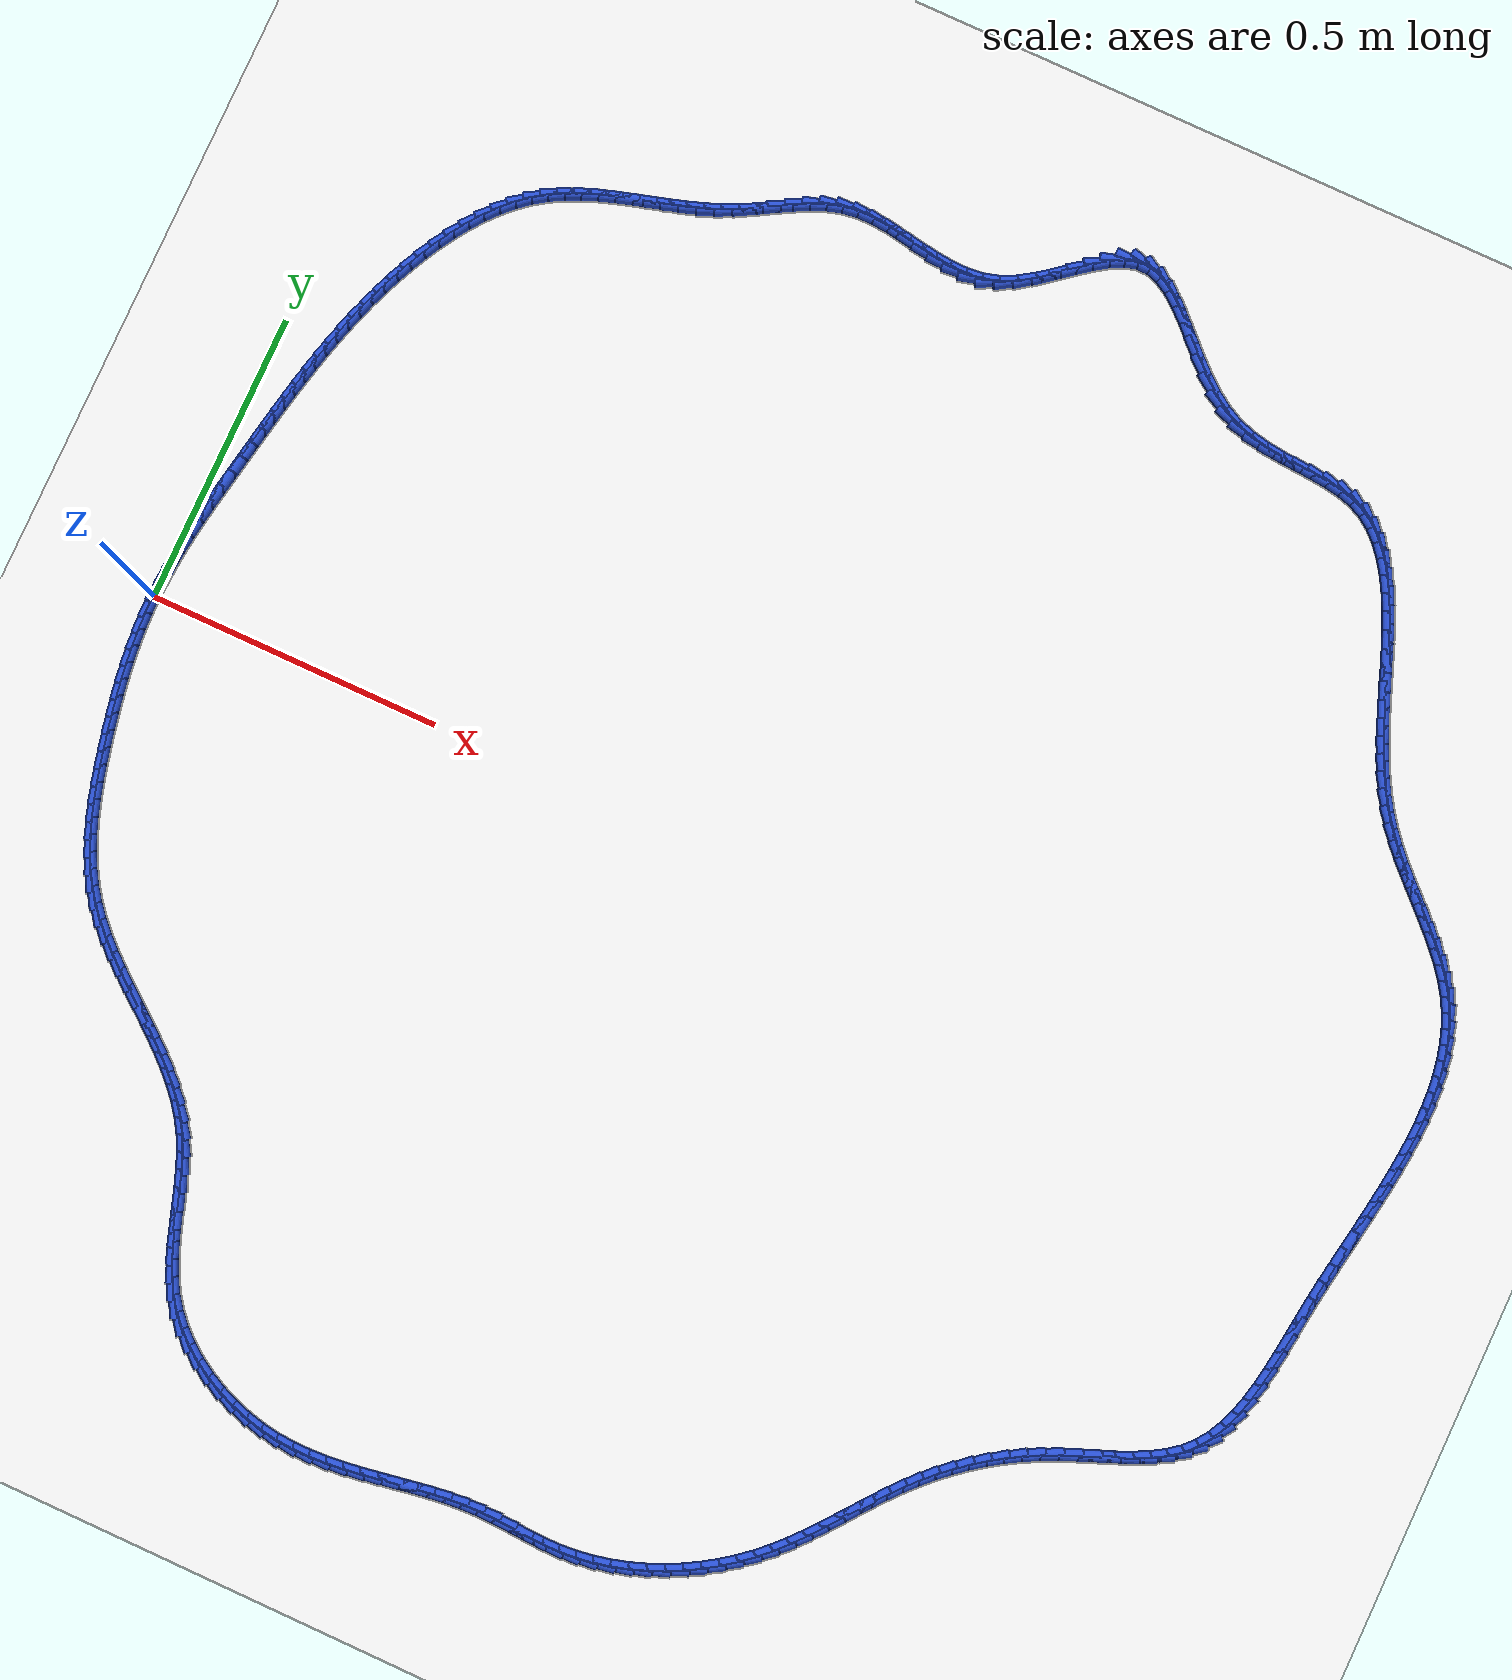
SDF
<sdf version="1.6">
 <world name="default">
  <light name="sun" type="directional">
   <pose>0 0 10 0 -0 0</pose>
   <diffuse>0.8 0.8 0.8 1</diffuse>
   <specular>0.2 0.2 0.2 1</specular>
   <attenuation>
    <range>1000</range>
    <constant>0.9</constant>
    <linear>0.01</linear>
    <quadratic>0.001</quadratic>
   </attenuation>
   <direction>-0.5 0.1 -0.9</direction>
  </light>
  <model name="ground_plane">
   <static>1</static>
   <link name="link">
    <collision name="collision">
     <geometry><plane><normal>0 0 1</normal><size>100 100</size></plane></geometry>
     <surface><friction><ode><mu>100</mu><mu2>50</mu2></ode></friction></surface>
    </collision>
    <visual name="visual">
     <cast_shadows>0</cast_shadows>
     <geometry><plane><normal>0 0 1</normal><size>100 100</size></plane></geometry>
     <material>
      <script><uri>file://media/materials/scripts/gazebo.material</uri><name>Gazebo/WhiteGlow</name></script>
     </material>
    </visual>
   </link>
  </model>
  <gravity>0 0 -9.8</gravity>
  <magnetic_field>6e-06 2.3e-05 -4.2e-05</magnetic_field>
  <atmosphere type="adiabatic"/>
  <physics name="default_physics" default="0" type="ode">
   <max_step_size>0.001</max_step_size>
   <real_time_factor>1</real_time_factor>
   <real_time_update_rate>1000</real_time_update_rate>
  </physics>
  <scene><ambient>0.4 0.4 0.4 1</ambient><background>0.7 0.7 0.7 1</background><shadows>1</shadows></scene>
  <spherical_coordinates>
   <surface_model>EARTH_WGS84</surface_model>
   <latitude_deg>0</latitude_deg>
   <longitude_deg>0</longitude_deg>
   <elevation>0</elevation>
   <heading_deg>0</heading_deg>
  </spherical_coordinates>
  <model name="line">
   <link name="link_0">
    <pose>2.6020852139652106e-18 -1.249000902703301e-16 0.01 0 1.57 1.5399630987236792</pose>
    <collision name="collision">
     <geometry><cylinder><radius>0.01</radius><length>0.08</length></cylinder></geometry>
    </collision>
    <visual name="visual">
     <material>
      <script><name>Gazebo/Blue</name><uri>file://media/materials/scripts/gazebo.material</uri></script>
     </material>
     <geometry><cylinder><radius>0.01</radius><length>0.08</length></cylinder></geometry>
    </visual>
   </link>
   <link name="link_1">
    <pose>0.0008660622261048055 0.028079698793367122 0.01 0 1.57 1.5052058898935707</pose>
    <collision name="collision">
     <geometry><cylinder><radius>0.01</radius><length>0.08</length></cylinder></geometry>
    </collision>
    <visual name="visual">
     <material>
      <script><name>Gazebo/Blue</name><uri>file://media/materials/scripts/gazebo.material</uri></script>
     </material>
     <geometry><cylinder><radius>0.01</radius><length>0.08</length></cylinder></geometry>
    </visual>
   </link>
   <link name="link_2">
    <pose>0.0027115590458533156 0.05617601344190277 0.01 0 1.57 1.4752069059453266</pose>
    <collision name="collision">
     <geometry><cylinder><radius>0.01</radius><length>0.08</length></cylinder></geometry>
    </collision>
    <visual name="visual">
     <material>
      <script><name>Gazebo/Blue</name><uri>file://media/materials/scripts/gazebo.material</uri></script>
     </material>
     <geometry><cylinder><radius>0.01</radius><length>0.08</length></cylinder></geometry>
    </visual>
   </link>
   <link name="link_3">
    <pose>0.005406133760680554 0.08427915087893992 0.01 0 1.57 1.4499196222061872</pose>
    <collision name="collision">
     <geometry><cylinder><radius>0.01</radius><length>0.08</length></cylinder></geometry>
    </collision>
    <visual name="visual">
     <material>
      <script><name>Gazebo/Blue</name><uri>file://media/materials/scripts/gazebo.material</uri></script>
     </material>
     <geometry><cylinder><radius>0.01</radius><length>0.08</length></cylinder></geometry>
    </visual>
   </link>
   <link name="link_4">
    <pose>0.008819429672021525 0.11237931803781168 0.01 0 1.57 1.429277018206215</pose>
    <collision name="collision">
     <geometry><cylinder><radius>0.01</radius><length>0.08</length></cylinder></geometry>
    </collision>
    <visual name="visual">
     <material>
      <script><name>Gazebo/Blue</name><uri>file://media/materials/scripts/gazebo.material</uri></script>
     </material>
     <geometry><cylinder><radius>0.01</radius><length>0.08</length></cylinder></geometry>
    </visual>
   </link>
   <link name="link_5">
    <pose>0.012821090081311251 0.1404667218518511 0.01 0 1.57 1.4132080930097983</pose>
    <collision name="collision">
     <geometry><cylinder><radius>0.01</radius><length>0.08</length></cylinder></geometry>
    </collision>
    <visual name="visual">
     <material>
      <script><name>Gazebo/Blue</name><uri>file://media/materials/scripts/gazebo.material</uri></script>
     </material>
     <geometry><cylinder><radius>0.01</radius><length>0.08</length></cylinder></geometry>
    </visual>
   </link>
   <link name="link_6">
    <pose>0.017280758289984738 0.16853156925439136 0.01 0 1.57 1.4016506264299584</pose>
    <collision name="collision">
     <geometry><cylinder><radius>0.01</radius><length>0.08</length></cylinder></geometry>
    </collision>
    <visual name="visual">
     <material>
      <script><name>Gazebo/Blue</name><uri>file://media/materials/scripts/gazebo.material</uri></script>
     </material>
     <geometry><cylinder><radius>0.01</radius><length>0.08</length></cylinder></geometry>
    </visual>
   </link>
   <link name="link_7">
    <pose>0.022068077599477005 0.19656406717876554 0.01 0 1.57 1.3945605944642037</pose>
    <collision name="collision">
     <geometry><cylinder><radius>0.01</radius><length>0.08</length></cylinder></geometry>
    </collision>
    <visual name="visual">
     <material>
      <script><name>Gazebo/Blue</name><uri>file://media/materials/scripts/gazebo.material</uri></script>
     </material>
     <geometry><cylinder><radius>0.01</radius><length>0.08</length></cylinder></geometry>
    </visual>
   </link>
   <link name="link_8">
    <pose>0.02705269131122306 0.22455442255830668 0.01 0 1.57 1.3919158162979768</pose>
    <collision name="collision">
     <geometry><cylinder><radius>0.01</radius><length>0.08</length></cylinder></geometry>
    </collision>
    <visual name="visual">
     <material>
      <script><name>Gazebo/Blue</name><uri>file://media/materials/scripts/gazebo.material</uri></script>
     </material>
     <geometry><cylinder><radius>0.01</radius><length>0.08</length></cylinder></geometry>
    </visual>
   </link>
   <link name="link_9">
    <pose>0.03210432701656352 0.2524928449966981 0.01 0 1.57 1.392048186569597</pose>
    <collision name="collision">
     <geometry><cylinder><radius>0.01</radius><length>0.08</length></cylinder></geometry>
    </collision>
    <visual name="visual">
     <material>
      <script><name>Gazebo/Blue</name><uri>file://media/materials/scripts/gazebo.material</uri></script>
     </material>
     <geometry><cylinder><radius>0.01</radius><length>0.08</length></cylinder></geometry>
    </visual>
   </link>
   <link name="link_10">
    <pose>0.03714126967113841 0.280371082421401 0.01 0 1.57 1.390479154712693</pose>
    <collision name="collision">
     <geometry><cylinder><radius>0.01</radius><length>0.08</length></cylinder></geometry>
    </collision>
    <visual name="visual">
     <material>
      <script><name>Gazebo/Blue</name><uri>file://media/materials/scripts/gazebo.material</uri></script>
     </material>
     <geometry><cylinder><radius>0.01</radius><length>0.08</length></cylinder></geometry>
    </visual>
   </link>
   <link name="link_11">
    <pose>0.04221166903717234 0.3081849969477614 0.01 0 1.57 1.3864552922551783</pose>
    <collision name="collision">
     <geometry><cylinder><radius>0.01</radius><length>0.08</length></cylinder></geometry>
    </collision>
    <visual name="visual">
     <material>
      <script><name>Gazebo/Blue</name><uri>file://media/materials/scripts/gazebo.material</uri></script>
     </material>
     <geometry><cylinder><radius>0.01</radius><length>0.08</length></cylinder></geometry>
    </visual>
   </link>
   <link name="link_12">
    <pose>0.04738515444702214 0.3359311311756189 0.01 0 1.57 1.3799682213017315</pose>
    <collision name="collision">
     <geometry><cylinder><radius>0.01</radius><length>0.08</length></cylinder></geometry>
    </collision>
    <visual name="visual">
     <material>
      <script><name>Gazebo/Blue</name><uri>file://media/materials/scripts/gazebo.material</uri></script>
     </material>
     <geometry><cylinder><radius>0.01</radius><length>0.08</length></cylinder></geometry>
    </visual>
   </link>
   <link name="link_13">
    <pose>0.05273135523304461 0.3636060277048135 0.01 0 1.57 1.3710153190737986</pose>
    <collision name="collision">
     <geometry><cylinder><radius>0.01</radius><length>0.08</length></cylinder></geometry>
    </collision>
    <visual name="visual">
     <material>
      <script><name>Gazebo/Blue</name><uri>file://media/materials/scripts/gazebo.material</uri></script>
     </material>
     <geometry><cylinder><radius>0.01</radius><length>0.08</length></cylinder></geometry>
    </visual>
   </link>
   <link name="link_14">
    <pose>0.05831990072759662 0.3912062291351849 0.01 0 1.57 1.359600944796768</pose>
    <collision name="collision">
     <geometry><cylinder><radius>0.01</radius><length>0.08</length></cylinder></geometry>
    </collision>
    <visual name="visual">
     <material>
      <script><name>Gazebo/Blue</name><uri>file://media/materials/scripts/gazebo.material</uri></script>
     </material>
     <geometry><cylinder><radius>0.01</radius><length>0.08</length></cylinder></geometry>
    </visual>
   </link>
   <link name="link_15">
    <pose>0.06422042026303498 0.4187282780665728 0.01 0 1.57 1.3457380730642046</pose>
    <collision name="collision">
     <geometry><cylinder><radius>0.01</radius><length>0.08</length></cylinder></geometry>
    </collision>
    <visual name="visual">
     <material>
      <script><name>Gazebo/Blue</name><uri>file://media/materials/scripts/gazebo.material</uri></script>
     </material>
     <geometry><cylinder><radius>0.01</radius><length>0.08</length></cylinder></geometry>
    </visual>
   </link>
   <link name="link_16">
    <pose>0.07050254317171657 0.44616871709881734 0.01 0 1.57 1.329450292412137</pose>
    <collision name="collision">
     <geometry><cylinder><radius>0.01</radius><length>0.08</length></cylinder></geometry>
    </collision>
    <visual name="visual">
     <material>
      <script><name>Gazebo/Blue</name><uri>file://media/materials/scripts/gazebo.material</uri></script>
     </material>
     <geometry><cylinder><radius>0.01</radius><length>0.08</length></cylinder></geometry>
    </visual>
   </link>
   <link name="link_17">
    <pose>0.07723589878599818 0.4735240888317581 0.01 0 1.57 1.3107740993499721</pose>
    <collision name="collision">
     <geometry><cylinder><radius>0.01</radius><length>0.08</length></cylinder></geometry>
    </collision>
    <visual name="visual">
     <material>
      <script><name>Gazebo/Blue</name><uri>file://media/materials/scripts/gazebo.material</uri></script>
     </material>
     <geometry><cylinder><radius>0.01</radius><length>0.08</length></cylinder></geometry>
    </visual>
   </link>
   <link name="link_18">
    <pose>0.08449011643823662 0.500790935865235 0.01 0 1.57 1.2897613835054031</pose>
    <collision name="collision">
     <geometry><cylinder><radius>0.01</radius><length>0.08</length></cylinder></geometry>
    </collision>
    <visual name="visual">
     <material>
      <script><name>Gazebo/Blue</name><uri>file://media/materials/scripts/gazebo.material</uri></script>
     </material>
     <geometry><cylinder><radius>0.01</radius><length>0.08</length></cylinder></geometry>
    </visual>
   </link>
   <link name="link_19">
    <pose>0.09233482546078875 0.5279658007990877 0.01 0 1.57 1.2664819603515456</pose>
    <collision name="collision">
     <geometry><cylinder><radius>0.01</radius><length>0.08</length></cylinder></geometry>
    </collision>
    <visual name="visual">
     <material>
      <script><name>Gazebo/Blue</name><uri>file://media/materials/scripts/gazebo.material</uri></script>
     </material>
     <geometry><cylinder><radius>0.01</radius><length>0.08</length></cylinder></geometry>
    </visual>
   </link>
   <link name="link_20">
    <pose>0.10083965518601146 0.5550452262331563 0.01 0 1.57 1.2410259676231075</pose>
    <collision name="collision">
     <geometry><cylinder><radius>0.01</radius><length>0.08</length></cylinder></geometry>
    </collision>
    <visual name="visual">
     <material>
      <script><name>Gazebo/Blue</name><uri>file://media/materials/scripts/gazebo.material</uri></script>
     </material>
     <geometry><cylinder><radius>0.01</radius><length>0.08</length></cylinder></geometry>
    </visual>
   </link>
   <link name="link_21">
    <pose>0.11007423494626148 0.5820257547672804 0.01 0 1.57 1.213505905597015</pose>
    <collision name="collision">
     <geometry><cylinder><radius>0.01</radius><length>0.08</length></cylinder></geometry>
    </collision>
    <visual name="visual">
     <material>
      <script><name>Gazebo/Blue</name><uri>file://media/materials/scripts/gazebo.material</uri></script>
     </material>
     <geometry><cylinder><radius>0.01</radius><length>0.08</length></cylinder></geometry>
    </visual>
   </link>
   <link name="link_22">
    <pose>0.12010819407389567 0.6089039290012996 0.01 0 1.57 1.1840580774979754</pose>
    <collision name="collision">
     <geometry><cylinder><radius>0.01</radius><length>0.08</length></cylinder></geometry>
    </collision>
    <visual name="visual">
     <material>
      <script><name>Gazebo/Blue</name><uri>file://media/materials/scripts/gazebo.material</uri></script>
     </material>
     <geometry><cylinder><radius>0.01</radius><length>0.08</length></cylinder></geometry>
    </visual>
   </link>
   <link name="link_23">
    <pose>0.13101116190127096 0.6356762915350543 0.01 0 1.57 1.152740916086234</pose>
    <collision name="collision">
     <geometry><cylinder><radius>0.01</radius><length>0.08</length></cylinder></geometry>
    </collision>
    <visual name="visual">
     <material>
      <script><name>Gazebo/Blue</name><uri>file://media/materials/scripts/gazebo.material</uri></script>
     </material>
     <geometry><cylinder><radius>0.01</radius><length>0.08</length></cylinder></geometry>
    </visual>
   </link>
   <link name="link_24">
    <pose>0.1428518289451667 0.662329922673893 0.01 0 1.57 1.1181642113383816</pose>
    <collision name="collision">
     <geometry><cylinder><radius>0.01</radius><length>0.08</length></cylinder></geometry>
    </collision>
    <visual name="visual">
     <material>
      <script><name>Gazebo/Blue</name><uri>file://media/materials/scripts/gazebo.material</uri></script>
     </material>
     <geometry><cylinder><radius>0.01</radius><length>0.08</length></cylinder></geometry>
    </visual>
   </link>
   <link name="link_25">
    <pose>0.15568588337482905 0.6887208524462017 0.01 0 1.57 1.078843472302882</pose>
    <collision name="collision">
     <geometry><cylinder><radius>0.01</radius><length>0.08</length></cylinder></geometry>
    </collision>
    <visual name="visual">
     <material>
      <script><name>Gazebo/Blue</name><uri>file://media/materials/scripts/gazebo.material</uri></script>
     </material>
     <geometry><cylinder><radius>0.01</radius><length>0.08</length></cylinder></geometry>
    </visual>
   </link>
   <link name="link_26">
    <pose>0.16955951309005005 0.7146093579449831 0.01 0 1.57 1.0341086229439806</pose>
    <collision name="collision">
     <geometry><cylinder><radius>0.01</radius><length>0.08</length></cylinder></geometry>
    </collision>
    <visual name="visual">
     <material>
      <script><name>Gazebo/Blue</name><uri>file://media/materials/scripts/gazebo.material</uri></script>
     </material>
     <geometry><cylinder><radius>0.01</radius><length>0.08</length></cylinder></geometry>
    </visual>
   </link>
   <link name="link_27">
    <pose>0.1845186892841949 0.7397535320855616 0.01 0 1.57 0.983212142931281</pose>
    <collision name="collision">
     <geometry><cylinder><radius>0.01</radius><length>0.08</length></cylinder></geometry>
    </collision>
    <visual name="visual">
     <material>
      <script><name>Gazebo/Blue</name><uri>file://media/materials/scripts/gazebo.material</uri></script>
     </material>
     <geometry><cylinder><radius>0.01</radius><length>0.08</length></cylinder></geometry>
    </visual>
   </link>
   <link name="link_28">
    <pose>0.200609383150629 0.763911467783262 0.01 0 1.57 0.9253209097011896</pose>
    <collision name="collision">
     <geometry><cylinder><radius>0.01</radius><length>0.08</length></cylinder></geometry>
    </collision>
    <visual name="visual">
     <material>
      <script><name>Gazebo/Blue</name><uri>file://media/materials/scripts/gazebo.material</uri></script>
     </material>
     <geometry><cylinder><radius>0.01</radius><length>0.08</length></cylinder></geometry>
    </visual>
   </link>
   <link name="link_29">
    <pose>0.21787756588271756 0.7868412579534092 0.01 0 1.57 0.8595546018502556</pose>
    <collision name="collision">
     <geometry><cylinder><radius>0.01</radius><length>0.08</length></cylinder></geometry>
    </collision>
    <visual name="visual">
     <material>
      <script><name>Gazebo/Blue</name><uri>file://media/materials/scripts/gazebo.material</uri></script>
     </material>
     <geometry><cylinder><radius>0.01</radius><length>0.08</length></cylinder></geometry>
    </visual>
   </link>
   <link name="link_30">
    <pose>0.23636920867382583 0.8083009955113277 0.01 0 1.57 0.7850616266130185</pose>
    <collision name="collision">
     <geometry><cylinder><radius>0.01</radius><length>0.08</length></cylinder></geometry>
    </collision>
    <visual name="visual">
     <material>
      <script><name>Gazebo/Blue</name><uri>file://media/materials/scripts/gazebo.material</uri></script>
     </material>
     <geometry><cylinder><radius>0.01</radius><length>0.08</length></cylinder></geometry>
    </visual>
   </link>
   <link name="link_31">
    <pose>0.25613028271731925 0.8280487733723427 0.01 0 1.57 0.701149060561529</pose>
    <collision name="collision">
     <geometry><cylinder><radius>0.01</radius><length>0.08</length></cylinder></geometry>
    </collision>
    <visual name="visual">
     <material>
      <script><name>Gazebo/Blue</name><uri>file://media/materials/scripts/gazebo.material</uri></script>
     </material>
     <geometry><cylinder><radius>0.01</radius><length>0.08</length></cylinder></geometry>
    </visual>
   </link>
   <link name="link_32">
    <pose>0.27720675920656296 0.8458426844517787 0.01 0 1.57 0.6076879779926697</pose>
    <collision name="collision">
     <geometry><cylinder><radius>0.01</radius><length>0.08</length></cylinder></geometry>
    </collision>
    <visual name="visual">
     <material>
      <script><name>Gazebo/Blue</name><uri>file://media/materials/scripts/gazebo.material</uri></script>
     </material>
     <geometry><cylinder><radius>0.01</radius><length>0.08</length></cylinder></geometry>
    </visual>
   </link>
   <link name="link_33">
    <pose>0.2996424998387554 0.8614463604788467 0.01 0 1.57 0.5145400947235713</pose>
    <collision name="collision">
     <geometry><cylinder><radius>0.01</radius><length>0.08</length></cylinder></geometry>
    </collision>
    <visual name="visual">
     <material>
      <script><name>Gazebo/Blue</name><uri>file://media/materials/scripts/gazebo.material</uri></script>
     </material>
     <geometry><cylinder><radius>0.01</radius><length>0.08</length></cylinder></geometry>
    </visual>
   </link>
   <link name="link_34">
    <pose>0.32338739491439905 0.8748701698609983 0.01 0 1.57 0.436171864998613</pose>
    <collision name="collision">
     <geometry><cylinder><radius>0.01</radius><length>0.08</length></cylinder></geometry>
    </collision>
    <visual name="visual">
     <material>
      <script><name>Gazebo/Blue</name><uri>file://media/materials/scripts/gazebo.material</uri></script>
     </material>
     <geometry><cylinder><radius>0.01</radius><length>0.08</length></cylinder></geometry>
    </visual>
   </link>
   <link name="link_35">
    <pose>0.3482618510657596 0.8864644607368619 0.01 0 1.57 0.37427692011915925</pose>
    <collision name="collision">
     <geometry><cylinder><radius>0.01</radius><length>0.08</length></cylinder></geometry>
    </collision>
    <visual name="visual">
     <material>
      <script><name>Gazebo/Blue</name><uri>file://media/materials/scripts/gazebo.material</uri></script>
     </material>
     <geometry><cylinder><radius>0.01</radius><length>0.08</length></cylinder></geometry>
    </visual>
   </link>
   <link name="link_36">
    <pose>0.37407683338930503 0.8966043714819051 0.01 0 1.57 0.3286852421767178</pose>
    <collision name="collision">
     <geometry><cylinder><radius>0.01</radius><length>0.08</length></cylinder></geometry>
    </collision>
    <visual name="visual">
     <material>
      <script><name>Gazebo/Blue</name><uri>file://media/materials/scripts/gazebo.material</uri></script>
     </material>
     <geometry><cylinder><radius>0.01</radius><length>0.08</length></cylinder></geometry>
    </visual>
   </link>
   <link name="link_37">
    <pose>0.40064330698150313 0.9056650404715947 0.01 0 1.57 0.29880877972297987</pose>
    <collision name="collision">
     <geometry><cylinder><radius>0.01</radius><length>0.08</length></cylinder></geometry>
    </collision>
    <visual name="visual">
     <material>
      <script><name>Gazebo/Blue</name><uri>file://media/materials/scripts/gazebo.material</uri></script>
     </material>
     <geometry><cylinder><radius>0.01</radius><length>0.08</length></cylinder></geometry>
    </visual>
   </link>
   <link name="link_38">
    <pose>0.42777223693882266 0.9140216060813987 0.01 0 1.57 0.2839978853599156</pose>
    <collision name="collision">
     <geometry><cylinder><radius>0.01</radius><length>0.08</length></cylinder></geometry>
    </collision>
    <visual name="visual">
     <material>
      <script><name>Gazebo/Blue</name><uri>file://media/materials/scripts/gazebo.material</uri></script>
     </material>
     <geometry><cylinder><radius>0.01</radius><length>0.08</length></cylinder></geometry>
    </visual>
   </link>
   <link name="link_39">
    <pose>0.45527458835773127 0.922049206686784 0.01 0 1.57 0.2837433595560888</pose>
    <collision name="collision">
     <geometry><cylinder><radius>0.01</radius><length>0.08</length></cylinder></geometry>
    </collision>
    <visual name="visual">
     <material>
      <script><name>Gazebo/Blue</name><uri>file://media/materials/scripts/gazebo.material</uri></script>
     </material>
     <geometry><cylinder><radius>0.01</radius><length>0.08</length></cylinder></geometry>
    </visual>
   </link>
   <link name="link_40">
    <pose>0.4829613263346972 0.9301229806632175 0.01 0 1.57 0.2977569081685537</pose>
    <collision name="collision">
     <geometry><cylinder><radius>0.01</radius><length>0.08</length></cylinder></geometry>
    </collision>
    <visual name="visual">
     <material>
      <script><name>Gazebo/Blue</name><uri>file://media/materials/scripts/gazebo.material</uri></script>
     </material>
     <geometry><cylinder><radius>0.01</radius><length>0.08</length></cylinder></geometry>
    </visual>
   </link>
   <link name="link_41">
    <pose>0.5106434159661885 0.9386180663861671 0.01 0 1.57 0.3259594965262889</pose>
    <collision name="collision">
     <geometry><cylinder><radius>0.01</radius><length>0.08</length></cylinder></geometry>
    </collision>
    <visual name="visual">
     <material>
      <script><name>Gazebo/Blue</name><uri>file://media/materials/scripts/gazebo.material</uri></script>
     </material>
     <geometry><cylinder><radius>0.01</radius><length>0.08</length></cylinder></geometry>
    </visual>
   </link>
   <link name="link_42">
    <pose>0.5381318223486733 0.9479096022310995 0.01 0 1.57 0.3683900130742555</pose>
    <collision name="collision">
     <geometry><cylinder><radius>0.01</radius><length>0.08</length></cylinder></geometry>
    </collision>
    <visual name="visual">
     <material>
      <script><name>Gazebo/Blue</name><uri>file://media/materials/scripts/gazebo.material</uri></script>
     </material>
     <geometry><cylinder><radius>0.01</radius><length>0.08</length></cylinder></geometry>
    </visual>
   </link>
   <link name="link_43">
    <pose>0.5652375105786197 0.9583727265734825 0.01 0 1.57 0.4250229659217246</pose>
    <collision name="collision">
     <geometry><cylinder><radius>0.01</radius><length>0.08</length></cylinder></geometry>
    </collision>
    <visual name="visual">
     <material>
      <script><name>Gazebo/Blue</name><uri>file://media/materials/scripts/gazebo.material</uri></script>
     </material>
     <geometry><cylinder><radius>0.01</radius><length>0.08</length></cylinder></geometry>
    </visual>
   </link>
   <link name="link_44">
    <pose>0.5917715325226953 0.9703823120772729 0.01 0 1.57 0.48482583229953596</pose>
    <collision name="collision">
     <geometry><cylinder><radius>0.01</radius><length>0.08</length></cylinder></geometry>
    </collision>
    <visual name="visual">
     <material>
      <script><name>Gazebo/Blue</name><uri>file://media/materials/scripts/gazebo.material</uri></script>
     </material>
     <geometry><cylinder><radius>0.01</radius><length>0.08</length></cylinder></geometry>
    </visual>
   </link>
   <link name="link_45">
    <pose>0.6176437182639088 0.9840107484211857 0.01 0 1.57 0.5166696406512757</pose>
    <collision name="collision">
     <geometry><cylinder><radius>0.01</radius><length>0.08</length></cylinder></geometry>
    </collision>
    <visual name="visual">
     <material>
      <script><name>Gazebo/Blue</name><uri>file://media/materials/scripts/gazebo.material</uri></script>
     </material>
     <geometry><cylinder><radius>0.01</radius><length>0.08</length></cylinder></geometry>
    </visual>
   </link>
   <link name="link_46">
    <pose>0.6430524878871661 0.9984466923262147 0.01 0 1.57 0.5153607486543597</pose>
    <collision name="collision">
     <geometry><cylinder><radius>0.01</radius><length>0.08</length></cylinder></geometry>
    </collision>
    <visual name="visual">
     <material>
      <script><name>Gazebo/Blue</name><uri>file://media/materials/scripts/gazebo.material</uri></script>
     </material>
     <geometry><cylinder><radius>0.01</radius><length>0.08</length></cylinder></geometry>
    </visual>
   </link>
   <link name="link_47">
    <pose>0.6682486837446736 1.0127182707478488 0.01 0 1.57 0.4799377684791751</pose>
    <collision name="collision">
     <geometry><cylinder><radius>0.01</radius><length>0.08</length></cylinder></geometry>
    </collision>
    <visual name="visual">
     <material>
      <script><name>Gazebo/Blue</name><uri>file://media/materials/scripts/gazebo.material</uri></script>
     </material>
     <geometry><cylinder><radius>0.01</radius><length>0.08</length></cylinder></geometry>
    </visual>
   </link>
   <link name="link_48">
    <pose>0.6934831481886377 1.0258536106415768 0.01 0 1.57 0.4078192004718096</pose>
    <collision name="collision">
     <geometry><cylinder><radius>0.01</radius><length>0.08</length></cylinder></geometry>
    </collision>
    <visual name="visual">
     <material>
      <script><name>Gazebo/Blue</name><uri>file://media/materials/scripts/gazebo.material</uri></script>
     </material>
     <geometry><cylinder><radius>0.01</radius><length>0.08</length></cylinder></geometry>
    </visual>
   </link>
   <link name="link_49">
    <pose>0.7190067235712646 1.0368808389628883 0.01 0 1.57 0.29596275547812606</pose>
    <collision name="collision">
     <geometry><cylinder><radius>0.01</radius><length>0.08</length></cylinder></geometry>
    </collision>
    <visual name="visual">
     <material>
      <script><name>Gazebo/Blue</name><uri>file://media/materials/scripts/gazebo.material</uri></script>
     </material>
     <geometry><cylinder><radius>0.01</radius><length>0.08</length></cylinder></geometry>
    </visual>
   </link>
   <link name="link_50">
    <pose>0.7450702522447605 1.044828082667271 0.01 0 1.57 0.14664558138641834</pose>
    <collision name="collision">
     <geometry><cylinder><radius>0.01</radius><length>0.08</length></cylinder></geometry>
    </collision>
    <visual name="visual">
     <material>
      <script><name>Gazebo/Blue</name><uri>file://media/materials/scripts/gazebo.material</uri></script>
     </material>
     <geometry><cylinder><radius>0.01</radius><length>0.08</length></cylinder></geometry>
    </visual>
   </link>
   <link name="link_51">
    <pose>0.7719098493120959 1.048792449615197 0.01 0 1.57 0.005772189447190347</pose>
    <collision name="collision">
     <geometry><cylinder><radius>0.01</radius><length>0.08</length></cylinder></geometry>
    </collision>
    <visual name="visual">
     <material>
      <script><name>Gazebo/Blue</name><uri>file://media/materials/scripts/gazebo.material</uri></script>
     </material>
     <geometry><cylinder><radius>0.01</radius><length>0.08</length></cylinder></geometry>
    </visual>
   </link>
   <link name="link_52">
    <pose>0.7995308737949642 1.048951885171942 0.01 0 1.57 -0.09220637235423118</pose>
    <collision name="collision">
     <geometry><cylinder><radius>0.01</radius><length>0.08</length></cylinder></geometry>
    </collision>
    <visual name="visual">
     <material>
      <script><name>Gazebo/Blue</name><uri>file://media/materials/scripts/gazebo.material</uri></script>
     </material>
     <geometry><cylinder><radius>0.01</radius><length>0.08</length></cylinder></geometry>
    </visual>
   </link>
   <link name="link_53">
    <pose>0.8277555781311013 1.0463419869138124 0.01 0 1.57 -0.14968195095804063</pose>
    <collision name="collision">
     <geometry><cylinder><radius>0.01</radius><length>0.08</length></cylinder></geometry>
    </collision>
    <visual name="visual">
     <material>
      <script><name>Gazebo/Blue</name><uri>file://media/materials/scripts/gazebo.material</uri></script>
     </material>
     <geometry><cylinder><radius>0.01</radius><length>0.08</length></cylinder></geometry>
    </visual>
   </link>
   <link name="link_54">
    <pose>0.8564011775090994 1.0420219463686466 0.01 0 1.57 -0.1704339877435066</pose>
    <collision name="collision">
     <geometry><cylinder><radius>0.01</radius><length>0.08</length></cylinder></geometry>
    </collision>
    <visual name="visual">
     <material>
      <script><name>Gazebo/Blue</name><uri>file://media/materials/scripts/gazebo.material</uri></script>
     </material>
     <geometry><cylinder><radius>0.01</radius><length>0.08</length></cylinder></geometry>
    </visual>
   </link>
   <link name="link_55">
    <pose>0.8852848871175495 1.0370509550642826 0.01 0 1.57 -0.15638033612341326</pose>
    <collision name="collision">
     <geometry><cylinder><radius>0.01</radius><length>0.08</length></cylinder></geometry>
    </collision>
    <visual name="visual">
     <material>
      <script><name>Gazebo/Blue</name><uri>file://media/materials/scripts/gazebo.material</uri></script>
     </material>
     <geometry><cylinder><radius>0.01</radius><length>0.08</length></cylinder></geometry>
    </visual>
   </link>
   <link name="link_56">
    <pose>0.9142239221450437 1.0324882045285588 0.01 0 1.57 -0.10702265904177997</pose>
    <collision name="collision">
     <geometry><cylinder><radius>0.01</radius><length>0.08</length></cylinder></geometry>
    </collision>
    <visual name="visual">
     <material>
      <script><name>Gazebo/Blue</name><uri>file://media/materials/scripts/gazebo.material</uri></script>
     </material>
     <geometry><cylinder><radius>0.01</radius><length>0.08</length></cylinder></geometry>
    </visual>
   </link>
   <link name="link_57">
    <pose>0.9430354977801729 1.029392886289313 0.01 0 1.57 -0.01995061046230502</pose>
    <collision name="collision">
     <geometry><cylinder><radius>0.01</radius><length>0.08</length></cylinder></geometry>
    </collision>
    <visual name="visual">
     <material>
      <script><name>Gazebo/Blue</name><uri>file://media/materials/scripts/gazebo.material</uri></script>
     </material>
     <geometry><cylinder><radius>0.01</radius><length>0.08</length></cylinder></geometry>
    </visual>
   </link>
   <link name="link_58">
    <pose>0.9715368292115285 1.028824191874383 0.01 0 1.57 0.10730858101633262</pose>
    <collision name="collision">
     <geometry><cylinder><radius>0.01</radius><length>0.08</length></cylinder></geometry>
    </collision>
    <visual name="visual">
     <material>
      <script><name>Gazebo/Blue</name><uri>file://media/materials/scripts/gazebo.material</uri></script>
     </material>
     <geometry><cylinder><radius>0.01</radius><length>0.08</length></cylinder></geometry>
    </visual>
   </link>
   <link name="link_59">
    <pose>0.9995451316277022 1.0318413128116073 0.01 0 1.57 0.27328906858868746</pose>
    <collision name="collision">
     <geometry><cylinder><radius>0.01</radius><length>0.08</length></cylinder></geometry>
    </collision>
    <visual name="visual">
     <material>
      <script><name>Gazebo/Blue</name><uri>file://media/materials/scripts/gazebo.material</uri></script>
     </material>
     <geometry><cylinder><radius>0.01</radius><length>0.08</length></cylinder></geometry>
    </visual>
   </link>
   <link name="link_60">
    <pose>1.0268776876784893 1.0395026930481222 0.01 0 1.57 0.44809342578353123</pose>
    <collision name="collision">
     <geometry><cylinder><radius>0.01</radius><length>0.08</length></cylinder></geometry>
    </collision>
    <visual name="visual">
     <material>
      <script><name>Gazebo/Blue</name><uri>file://media/materials/scripts/gazebo.material</uri></script>
     </material>
     <geometry><cylinder><radius>0.01</radius><length>0.08</length></cylinder></geometry>
    </visual>
   </link>
   <link name="link_61">
    <pose>1.0534069448274923 1.0522554599802738 0.01 0 1.57 0.5718777276622412</pose>
    <collision name="collision">
     <geometry><cylinder><radius>0.01</radius><length>0.08</length></cylinder></geometry>
    </collision>
    <visual name="visual">
     <material>
      <script><name>Gazebo/Blue</name><uri>file://media/materials/scripts/gazebo.material</uri></script>
     </material>
     <geometry><cylinder><radius>0.01</radius><length>0.08</length></cylinder></geometry>
    </visual>
   </link>
   <link name="link_62">
    <pose>1.0791601967048152 1.0688307916904933 0.01 0 1.57 0.6449468357490047</pose>
    <collision name="collision">
     <geometry><cylinder><radius>0.01</radius><length>0.08</length></cylinder></geometry>
    </collision>
    <visual name="visual">
     <material>
      <script><name>Gazebo/Blue</name><uri>file://media/materials/scripts/gazebo.material</uri></script>
     </material>
     <geometry><cylinder><radius>0.01</radius><length>0.08</length></cylinder></geometry>
    </visual>
   </link>
   <link name="link_63">
    <pose>1.1041917038802125 1.0876610283717096 0.01 0 1.57 0.6753978885737065</pose>
    <collision name="collision">
     <geometry><cylinder><radius>0.01</radius><length>0.08</length></cylinder></geometry>
    </collision>
    <visual name="visual">
     <material>
      <script><name>Gazebo/Blue</name><uri>file://media/materials/scripts/gazebo.material</uri></script>
     </material>
     <geometry><cylinder><radius>0.01</radius><length>0.08</length></cylinder></geometry>
    </visual>
   </link>
   <link name="link_64">
    <pose>1.1285557269234388 1.107178510216852 0.01 0 1.57 0.6653369742243661</pose>
    <collision name="collision">
     <geometry><cylinder><radius>0.01</radius><length>0.08</length></cylinder></geometry>
    </collision>
    <visual name="visual">
     <material>
      <script><name>Gazebo/Blue</name><uri>file://media/materials/scripts/gazebo.material</uri></script>
     </material>
     <geometry><cylinder><radius>0.01</radius><length>0.08</length></cylinder></geometry>
    </visual>
   </link>
   <link name="link_65">
    <pose>1.1523065264042487 1.12581557741885 0.01 0 1.57 0.609414048286463</pose>
    <collision name="collision">
     <geometry><cylinder><radius>0.01</radius><length>0.08</length></cylinder></geometry>
    </collision>
    <visual name="visual">
     <material>
      <script><name>Gazebo/Blue</name><uri>file://media/materials/scripts/gazebo.material</uri></script>
     </material>
     <geometry><cylinder><radius>0.01</radius><length>0.08</length></cylinder></geometry>
    </visual>
   </link>
   <link name="link_66">
    <pose>1.175498362892397 1.1420045701706332 0.01 0 1.57 0.49247462118310764</pose>
    <collision name="collision">
     <geometry><cylinder><radius>0.01</radius><length>0.08</length></cylinder></geometry>
    </collision>
    <visual name="visual">
     <material>
      <script><name>Gazebo/Blue</name><uri>file://media/materials/scripts/gazebo.material</uri></script>
     </material>
     <geometry><cylinder><radius>0.01</radius><length>0.08</length></cylinder></geometry>
    </visual>
   </link>
   <link name="link_67">
    <pose>1.1981854969576382 1.15417782866513 0.01 0 1.57 0.2881056712653823</pose>
    <collision name="collision">
     <geometry><cylinder><radius>0.01</radius><length>0.08</length></cylinder></geometry>
    </collision>
    <visual name="visual">
     <material>
      <script><name>Gazebo/Blue</name><uri>file://media/materials/scripts/gazebo.material</uri></script>
     </material>
     <geometry><cylinder><radius>0.01</radius><length>0.08</length></cylinder></geometry>
    </visual>
   </link>
   <link name="link_68">
    <pose>1.220422189169727 1.160767693095271 0.01 0 1.57 -0.017070213978598474</pose>
    <collision name="collision">
     <geometry><cylinder><radius>0.01</radius><length>0.08</length></cylinder></geometry>
    </collision>
    <visual name="visual">
     <material>
      <script><name>Gazebo/Blue</name><uri>file://media/materials/scripts/gazebo.material</uri></script>
     </material>
     <geometry><cylinder><radius>0.01</radius><length>0.08</length></cylinder></geometry>
    </visual>
   </link>
   <link name="link_69">
    <pose>1.242270595344905 1.160394699896962 0.01 0 1.57 -0.3150210145547944</pose>
    <collision name="collision">
     <geometry><cylinder><radius>0.01</radius><length>0.08</length></cylinder></geometry>
    </collision>
    <visual name="visual">
     <material>
      <script><name>Gazebo/Blue</name><uri>file://media/materials/scripts/gazebo.material</uri></script>
     </material>
     <geometry><cylinder><radius>0.01</radius><length>0.08</length></cylinder></geometry>
    </visual>
   </link>
   <link name="link_70">
    <pose>1.2638633023680568 1.1533582263795796 0.01 0 1.57 -0.5271377800163405</pose>
    <collision name="collision">
     <geometry><cylinder><radius>0.01</radius><length>0.08</length></cylinder></geometry>
    </collision>
    <visual name="visual">
     <material>
      <script><name>Gazebo/Blue</name><uri>file://media/materials/scripts/gazebo.material</uri></script>
     </material>
     <geometry><cylinder><radius>0.01</radius><length>0.08</length></cylinder></geometry>
    </visual>
   </link>
   <link name="link_71">
    <pose>1.2853699008650052 1.1408396951481046 0.01 0 1.57 -0.6615853059170025</pose>
    <collision name="collision">
     <geometry><cylinder><radius>0.01</radius><length>0.08</length></cylinder></geometry>
    </collision>
    <visual name="visual">
     <material>
      <script><name>Gazebo/Blue</name><uri>file://media/materials/scripts/gazebo.material</uri></script>
     </material>
     <geometry><cylinder><radius>0.01</radius><length>0.08</length></cylinder></geometry>
    </visual>
   </link>
   <link name="link_72">
    <pose>1.3069603100398033 1.124028361012376 0.01 0 1.57 -0.7392312296707337</pose>
    <collision name="collision">
     <geometry><cylinder><radius>0.01</radius><length>0.08</length></cylinder></geometry>
    </collision>
    <visual name="visual">
     <material>
      <script><name>Gazebo/Blue</name><uri>file://media/materials/scripts/gazebo.material</uri></script>
     </material>
     <geometry><cylinder><radius>0.01</radius><length>0.08</length></cylinder></geometry>
    </visual>
   </link>
   <link name="link_73">
    <pose>1.3288044490965027 1.1041134787822344 0.01 0 1.57 -0.775451941982872</pose>
    <collision name="collision">
     <geometry><cylinder><radius>0.01</radius><length>0.08</length></cylinder></geometry>
    </collision>
    <visual name="visual">
     <material>
      <script><name>Gazebo/Blue</name><uri>file://media/materials/scripts/gazebo.material</uri></script>
     </material>
     <geometry><cylinder><radius>0.01</radius><length>0.08</length></cylinder></geometry>
    </visual>
   </link>
   <link name="link_74">
    <pose>1.3510722372391535 1.0822843032675165 0.01 0 1.57 -0.7786353338687526</pose>
    <collision name="collision">
     <geometry><cylinder><radius>0.01</radius><length>0.08</length></cylinder></geometry>
    </collision>
    <visual name="visual">
     <material>
      <script><name>Gazebo/Blue</name><uri>file://media/materials/scripts/gazebo.material</uri></script>
     </material>
     <geometry><cylinder><radius>0.01</radius><length>0.08</length></cylinder></geometry>
    </visual>
   </link>
   <link name="link_75">
    <pose>1.3739335936718093 1.059730089278063 0.01 0 1.57 -0.7518364163350696</pose>
    <collision name="collision">
     <geometry><cylinder><radius>0.01</radius><length>0.08</length></cylinder></geometry>
    </collision>
    <visual name="visual">
     <material>
      <script><name>Gazebo/Blue</name><uri>file://media/materials/scripts/gazebo.material</uri></script>
     </material>
     <geometry><cylinder><radius>0.01</radius><length>0.08</length></cylinder></geometry>
    </visual>
   </link>
   <link name="link_76">
    <pose>1.3975584375985204 1.0376400916237118 0.01 0 1.57 -0.6940486093549676</pose>
    <collision name="collision">
     <geometry><cylinder><radius>0.01</radius><length>0.08</length></cylinder></geometry>
    </collision>
    <visual name="visual">
     <material>
      <script><name>Gazebo/Blue</name><uri>file://media/materials/scripts/gazebo.material</uri></script>
     </material>
     <geometry><cylinder><radius>0.01</radius><length>0.08</length></cylinder></geometry>
    </visual>
   </link>
   <link name="link_77">
    <pose>1.4221166882233387 1.0172035651143025 0.01 0 1.57 -0.6010019453669507</pose>
    <collision name="collision">
     <geometry><cylinder><radius>0.01</radius><length>0.08</length></cylinder></geometry>
    </collision>
    <visual name="visual">
     <material>
      <script><name>Gazebo/Blue</name><uri>file://media/materials/scripts/gazebo.material</uri></script>
     </material>
     <geometry><cylinder><radius>0.01</radius><length>0.08</length></cylinder></geometry>
    </visual>
   </link>
   <link name="link_78">
    <pose>1.4477782647503157 0.9996097645596742 0.01 0 1.57 -0.4672737815228583</pose>
    <collision name="collision">
     <geometry><cylinder><radius>0.01</radius><length>0.08</length></cylinder></geometry>
    </collision>
    <visual name="visual">
     <material>
      <script><name>Gazebo/Blue</name><uri>file://media/materials/scripts/gazebo.material</uri></script>
     </material>
     <geometry><cylinder><radius>0.01</radius><length>0.08</length></cylinder></geometry>
    </visual>
   </link>
   <link name="link_79">
    <pose>1.4747065225168912 0.9860233553000808 0.01 0 1.57 -0.32056708417595814</pose>
    <collision name="collision">
     <geometry><cylinder><radius>0.01</radius><length>0.08</length></cylinder></geometry>
    </collision>
    <visual name="visual">
     <material>
      <script><name>Gazebo/Blue</name><uri>file://media/materials/scripts/gazebo.material</uri></script>
     </material>
     <geometry><cylinder><radius>0.01</radius><length>0.08</length></cylinder></geometry>
    </visual>
   </link>
   <link name="link_80">
    <pose>1.5028193322685846 0.976689371570524 0.01 0 1.57 -0.2050426987425711</pose>
    <collision name="collision">
     <geometry><cylinder><radius>0.01</radius><length>0.08</length></cylinder></geometry>
    </collision>
    <visual name="visual">
     <material>
      <script><name>Gazebo/Blue</name><uri>file://media/materials/scripts/gazebo.material</uri></script>
     </material>
     <geometry><cylinder><radius>0.01</radius><length>0.08</length></cylinder></geometry>
    </visual>
   </link>
   <link name="link_81">
    <pose>1.5317211644491149 0.9706787915739183 0.01 0 1.57 -0.12547350396702192</pose>
    <collision name="collision">
     <geometry><cylinder><radius>0.01</radius><length>0.08</length></cylinder></geometry>
    </collision>
    <visual name="visual">
     <material>
      <script><name>Gazebo/Blue</name><uri>file://media/materials/scripts/gazebo.material</uri></script>
     </material>
     <geometry><cylinder><radius>0.01</radius><length>0.08</length></cylinder></geometry>
    </visual>
   </link>
   <link name="link_82">
    <pose>1.560996087969309 0.9669861655626666 0.01 0 1.57 -0.08124234201683778</pose>
    <collision name="collision">
     <geometry><cylinder><radius>0.01</radius><length>0.08</length></cylinder></geometry>
    </collision>
    <visual name="visual">
     <material>
      <script><name>Gazebo/Blue</name><uri>file://media/materials/scripts/gazebo.material</uri></script>
     </material>
     <geometry><cylinder><radius>0.01</radius><length>0.08</length></cylinder></geometry>
    </visual>
   </link>
   <link name="link_83">
    <pose>1.590228171739994 0.9646060437891716 0.01 0 1.57 -0.0719239857612996</pose>
    <collision name="collision">
     <geometry><cylinder><radius>0.01</radius><length>0.08</length></cylinder></geometry>
    </collision>
    <visual name="visual">
     <material>
      <script><name>Gazebo/Blue</name><uri>file://media/materials/scripts/gazebo.material</uri></script>
     </material>
     <geometry><cylinder><radius>0.01</radius><length>0.08</length></cylinder></geometry>
    </visual>
   </link>
   <link name="link_84">
    <pose>1.6190014846719962 0.9625329765058358 0.01 0 1.57 -0.09901566003177574</pose>
    <collision name="collision">
     <geometry><cylinder><radius>0.01</radius><length>0.08</length></cylinder></geometry>
    </collision>
    <visual name="visual">
     <material>
      <script><name>Gazebo/Blue</name><uri>file://media/materials/scripts/gazebo.material</uri></script>
     </material>
     <geometry><cylinder><radius>0.01</radius><length>0.08</length></cylinder></geometry>
    </visual>
   </link>
   <link name="link_85">
    <pose>1.6469000956761444 0.9597615139650632 0.01 0 1.57 -0.166634555978437</pose>
    <collision name="collision">
     <geometry><cylinder><radius>0.01</radius><length>0.08</length></cylinder></geometry>
    </collision>
    <visual name="visual">
     <material>
      <script><name>Gazebo/Blue</name><uri>file://media/materials/scripts/gazebo.material</uri></script>
     </material>
     <geometry><cylinder><radius>0.01</radius><length>0.08</length></cylinder></geometry>
    </visual>
   </link>
   <link name="link_86">
    <pose>1.6735080736632633 0.9552862064192557 0.01 0 1.57 -0.28089341329585</pose>
    <collision name="collision">
     <geometry><cylinder><radius>0.01</radius><length>0.08</length></cylinder></geometry>
    </collision>
    <visual name="visual">
     <material>
      <script><name>Gazebo/Blue</name><uri>file://media/materials/scripts/gazebo.material</uri></script>
     </material>
     <geometry><cylinder><radius>0.01</radius><length>0.08</length></cylinder></geometry>
    </visual>
   </link>
   <link name="link_87">
    <pose>1.6984094875441818 0.9481016041208168 0.01 0 1.57 -0.44258007186875736</pose>
    <collision name="collision">
     <geometry><cylinder><radius>0.01</radius><length>0.08</length></cylinder></geometry>
    </collision>
    <visual name="visual">
     <material>
      <script><name>Gazebo/Blue</name><uri>file://media/materials/scripts/gazebo.material</uri></script>
     </material>
     <geometry><cylinder><radius>0.01</radius><length>0.08</length></cylinder></geometry>
    </visual>
   </link>
   <link name="link_88">
    <pose>1.721225843466963 0.9372881054609653 0.01 0 1.57 -0.6111173527483849</pose>
    <collision name="collision">
     <geometry><cylinder><radius>0.01</radius><length>0.08</length></cylinder></geometry>
    </collision>
    <visual name="visual">
     <material>
      <script><name>Gazebo/Blue</name><uri>file://media/materials/scripts/gazebo.material</uri></script>
     </material>
     <geometry><cylinder><radius>0.01</radius><length>0.08</length></cylinder></geometry>
    </visual>
   </link>
   <link name="link_89">
    <pose>1.7419471412663887 0.9227711096777925 0.01 0 1.57 -0.7578138614818415</pose>
    <collision name="collision">
     <geometry><cylinder><radius>0.01</radius><length>0.08</length></cylinder></geometry>
    </collision>
    <visual name="visual">
     <material>
      <script><name>Gazebo/Blue</name><uri>file://media/materials/scripts/gazebo.material</uri></script>
     </material>
     <geometry><cylinder><radius>0.01</radius><length>0.08</length></cylinder></geometry>
    </visual>
   </link>
   <link name="link_90">
    <pose>1.7607728513734862 0.9049563575663926 0.01 0 1.57 -0.8794606070302597</pose>
    <collision name="collision">
     <geometry><cylinder><radius>0.01</radius><length>0.08</length></cylinder></geometry>
    </collision>
    <visual name="visual">
     <material>
      <script><name>Gazebo/Blue</name><uri>file://media/materials/scripts/gazebo.material</uri></script>
     </material>
     <geometry><cylinder><radius>0.01</radius><length>0.08</length></cylinder></geometry>
    </visual>
   </link>
   <link name="link_91">
    <pose>1.7779048599772713 0.8842551295487773 0.01 0 1.57 -0.9771620518458581</pose>
    <collision name="collision">
     <geometry><cylinder><radius>0.01</radius><length>0.08</length></cylinder></geometry>
    </collision>
    <visual name="visual">
     <material>
      <script><name>Gazebo/Blue</name><uri>file://media/materials/scripts/gazebo.material</uri></script>
     </material>
     <geometry><cylinder><radius>0.01</radius><length>0.08</length></cylinder></geometry>
    </visual>
   </link>
   <link name="link_92">
    <pose>1.79354505326676 0.8610787060469575 0.01 0 1.57 -1.0538268053528062</pose>
    <collision name="collision">
     <geometry><cylinder><radius>0.01</radius><length>0.08</length></cylinder></geometry>
    </collision>
    <visual name="visual">
     <material>
      <script><name>Gazebo/Blue</name><uri>file://media/materials/scripts/gazebo.material</uri></script>
     </material>
     <geometry><cylinder><radius>0.01</radius><length>0.08</length></cylinder></geometry>
    </visual>
   </link>
   <link name="link_93">
    <pose>1.8078953174309684 0.8358383674829457 0.01 0 1.57 -1.1126451698235005</pose>
    <collision name="collision">
     <geometry><cylinder><radius>0.01</radius><length>0.08</length></cylinder></geometry>
    </collision>
    <visual name="visual">
     <material>
      <script><name>Gazebo/Blue</name><uri>file://media/materials/scripts/gazebo.material</uri></script>
     </material>
     <geometry><cylinder><radius>0.01</radius><length>0.08</length></cylinder></geometry>
    </visual>
   </link>
   <link name="link_94">
    <pose>1.8211575386589116 0.8089453942787533 0.01 0 1.57 -1.1563799704834994</pose>
    <collision name="collision">
     <geometry><cylinder><radius>0.01</radius><length>0.08</length></cylinder></geometry>
    </collision>
    <visual name="visual">
     <material>
      <script><name>Gazebo/Blue</name><uri>file://media/materials/scripts/gazebo.material</uri></script>
     </material>
     <geometry><cylinder><radius>0.01</radius><length>0.08</length></cylinder></geometry>
    </visual>
   </link>
   <link name="link_95">
    <pose>1.8335336031396063 0.7808110668563919 0.01 0 1.57 -1.1871380603355346</pose>
    <collision name="collision">
     <geometry><cylinder><radius>0.01</radius><length>0.08</length></cylinder></geometry>
    </collision>
    <visual name="visual">
     <material>
      <script><name>Gazebo/Blue</name><uri>file://media/materials/scripts/gazebo.material</uri></script>
     </material>
     <geometry><cylinder><radius>0.01</radius><length>0.08</length></cylinder></geometry>
    </visual>
   </link>
   <link name="link_96">
    <pose>1.845225397062068 0.7518466656378728 0.01 0 1.57 -1.2063475339395864</pose>
    <collision name="collision">
     <geometry><cylinder><radius>0.01</radius><length>0.08</length></cylinder></geometry>
    </collision>
    <visual name="visual">
     <material>
      <script><name>Gazebo/Blue</name><uri>file://media/materials/scripts/gazebo.material</uri></script>
     </material>
     <geometry><cylinder><radius>0.01</radius><length>0.08</length></cylinder></geometry>
    </visual>
   </link>
   <link name="link_97">
    <pose>1.856434806615312 0.7224634710452079 0.01 0 1.57 -1.2147908505844702</pose>
    <collision name="collision">
     <geometry><cylinder><radius>0.01</radius><length>0.08</length></cylinder></geometry>
    </collision>
    <visual name="visual">
     <material>
      <script><name>Gazebo/Blue</name><uri>file://media/materials/scripts/gazebo.material</uri></script>
     </material>
     <geometry><cylinder><radius>0.01</radius><length>0.08</length></cylinder></geometry>
    </visual>
   </link>
   <link name="link_98">
    <pose>1.8673637179883547 0.6930727635004088 0.01 0 1.57 -1.2126247387569489</pose>
    <collision name="collision">
     <geometry><cylinder><radius>0.01</radius><length>0.08</length></cylinder></geometry>
    </collision>
    <visual name="visual">
     <material>
      <script><name>Gazebo/Blue</name><uri>file://media/materials/scripts/gazebo.material</uri></script>
     </material>
     <geometry><cylinder><radius>0.01</radius><length>0.08</length></cylinder></geometry>
    </visual>
   </link>
   <link name="link_99">
    <pose>1.8782140173702122 0.6640858234254873 0.01 0 1.57 -1.1994061360290218</pose>
    <collision name="collision">
     <geometry><cylinder><radius>0.01</radius><length>0.08</length></cylinder></geometry>
    </collision>
    <visual name="visual">
     <material>
      <script><name>Gazebo/Blue</name><uri>file://media/materials/scripts/gazebo.material</uri></script>
     </material>
     <geometry><cylinder><radius>0.01</radius><length>0.08</length></cylinder></geometry>
    </visual>
   </link>
   <link name="link_100">
    <pose>1.8891878591452123 0.6359089958126027 0.01 0 1.57 -1.1760706897455728</pose>
    <collision name="collision">
     <geometry><cylinder><radius>0.01</radius><length>0.08</length></cylinder></geometry>
    </collision>
    <visual name="visual">
     <material>
      <script><name>Gazebo/Blue</name><uri>file://media/materials/scripts/gazebo.material</uri></script>
     </material>
     <geometry><cylinder><radius>0.01</radius><length>0.08</length></cylinder></geometry>
    </visual>
   </link>
   <link name="link_101">
    <pose>1.9004976167805088 0.6087605702929184 0.01 0 1.57 -1.1445607715036472</pose>
    <collision name="collision">
     <geometry><cylinder><radius>0.01</radius><length>0.08</length></cylinder></geometry>
    </collision>
    <visual name="visual">
     <material>
      <script><name>Gazebo/Blue</name><uri>file://media/materials/scripts/gazebo.material</uri></script>
     </material>
     <geometry><cylinder><radius>0.01</radius><length>0.08</length></cylinder></geometry>
    </visual>
   </link>
   <link name="link_102">
    <pose>1.9123688201610956 0.5826167272056716 0.01 0 1.57 -1.104942185150727</pose>
    <collision name="collision">
     <geometry><cylinder><radius>0.01</radius><length>0.08</length></cylinder></geometry>
    </collision>
    <visual name="visual">
     <material>
      <script><name>Gazebo/Blue</name><uri>file://media/materials/scripts/gazebo.material</uri></script>
     </material>
     <geometry><cylinder><radius>0.01</radius><length>0.08</length></cylinder></geometry>
    </visual>
   </link>
   <link name="link_103">
    <pose>1.9250278666147635 0.5574376838852674 0.01 0 1.57 -1.0574553291814013</pose>
    <collision name="collision">
     <geometry><cylinder><radius>0.01</radius><length>0.08</length></cylinder></geometry>
    </collision>
    <visual name="visual">
     <material>
      <script><name>Gazebo/Blue</name><uri>file://media/materials/scripts/gazebo.material</uri></script>
     </material>
     <geometry><cylinder><radius>0.01</radius><length>0.08</length></cylinder></geometry>
    </visual>
   </link>
   <link name="link_104">
    <pose>1.938701153469305 0.5331836576661113 0.01 0 1.57 -1.0027623030553932</pose>
    <collision name="collision">
     <geometry><cylinder><radius>0.01</radius><length>0.08</length></cylinder></geometry>
    </collision>
    <visual name="visual">
     <material>
      <script><name>Gazebo/Blue</name><uri>file://media/materials/scripts/gazebo.material</uri></script>
     </material>
     <geometry><cylinder><radius>0.01</radius><length>0.08</length></cylinder></geometry>
    </visual>
   </link>
   <link name="link_105">
    <pose>1.95361507805251 0.5098148658826085 0.01 0 1.57 -0.9419899139697636</pose>
    <collision name="collision">
     <geometry><cylinder><radius>0.01</radius><length>0.08</length></cylinder></geometry>
    </collision>
    <visual name="visual">
     <material>
      <script><name>Gazebo/Blue</name><uri>file://media/materials/scripts/gazebo.material</uri></script>
     </material>
     <geometry><cylinder><radius>0.01</radius><length>0.08</length></cylinder></geometry>
    </visual>
   </link>
   <link name="link_106">
    <pose>1.969996037692172 0.4872915258691639 0.01 0 1.57 -0.8789616196129737</pose>
    <collision name="collision">
     <geometry><cylinder><radius>0.01</radius><length>0.08</length></cylinder></geometry>
    </collision>
    <visual name="visual">
     <material>
      <script><name>Gazebo/Blue</name><uri>file://media/materials/scripts/gazebo.material</uri></script>
     </material>
     <geometry><cylinder><radius>0.01</radius><length>0.08</length></cylinder></geometry>
    </visual>
   </link>
   <link name="link_107">
    <pose>1.9879996825098296 0.4655591551772365 0.01 0 1.57 -0.8282208937337646</pose>
    <collision name="collision">
     <geometry><cylinder><radius>0.01</radius><length>0.08</length></cylinder></geometry>
    </collision>
    <visual name="visual">
     <material>
      <script><name>Gazebo/Blue</name><uri>file://media/materials/scripts/gazebo.material</uri></script>
     </material>
     <geometry><cylinder><radius>0.01</radius><length>0.08</length></cylinder></geometry>
    </visual>
   </link>
   <link name="link_108">
    <pose>2.0073521117737756 0.4444740197165348 0.01 0 1.57 -0.7939366253925281</pose>
    <collision name="collision">
     <geometry><cylinder><radius>0.01</radius><length>0.08</length></cylinder></geometry>
    </collision>
    <visual name="visual">
     <material>
      <script><name>Gazebo/Blue</name><uri>file://media/materials/scripts/gazebo.material</uri></script>
     </material>
     <geometry><cylinder><radius>0.01</radius><length>0.08</length></cylinder></geometry>
    </visual>
   </link>
   <link name="link_109">
    <pose>2.0276181785671854 0.4238588818275418 0.01 0 1.57 -0.7751266450777974</pose>
    <collision name="collision">
     <geometry><cylinder><radius>0.01</radius><length>0.08</length></cylinder></geometry>
    </collision>
    <visual name="visual">
     <material>
      <script><name>Gazebo/Blue</name><uri>file://media/materials/scripts/gazebo.material</uri></script>
     </material>
     <geometry><cylinder><radius>0.01</radius><length>0.08</length></cylinder></geometry>
    </visual>
   </link>
   <link name="link_110">
    <pose>2.0483624485415595 0.40353644412847745 0.01 0 1.57 -0.7712506253116056</pose>
    <collision name="collision">
     <geometry><cylinder><radius>0.01</radius><length>0.08</length></cylinder></geometry>
    </collision>
    <visual name="visual">
     <material>
      <script><name>Gazebo/Blue</name><uri>file://media/materials/scripts/gazebo.material</uri></script>
     </material>
     <geometry><cylinder><radius>0.01</radius><length>0.08</length></cylinder></geometry>
    </visual>
   </link>
   <link name="link_111">
    <pose>2.0691494873483993 0.3833294092375626 0.01 0 1.57 -0.7823132337479165</pose>
    <collision name="collision">
     <geometry><cylinder><radius>0.01</radius><length>0.08</length></cylinder></geometry>
    </collision>
    <visual name="visual">
     <material>
      <script><name>Gazebo/Blue</name><uri>file://media/materials/scripts/gazebo.material</uri></script>
     </material>
     <geometry><cylinder><radius>0.01</radius><length>0.08</length></cylinder></geometry>
    </visual>
   </link>
   <link name="link_112">
    <pose>2.089543860639204 0.3630604797730171 0.01 0 1.57 -0.8088963257406372</pose>
    <collision name="collision">
     <geometry><cylinder><radius>0.01</radius><length>0.08</length></cylinder></geometry>
    </collision>
    <visual name="visual">
     <material>
      <script><name>Gazebo/Blue</name><uri>file://media/materials/scripts/gazebo.material</uri></script>
     </material>
     <geometry><cylinder><radius>0.01</radius><length>0.08</length></cylinder></geometry>
    </visual>
   </link>
   <link name="link_113">
    <pose>2.109110134065473 0.342552358353061 0.01 0 1.57 -0.8521367463158239</pose>
    <collision name="collision">
     <geometry><cylinder><radius>0.01</radius><length>0.08</length></cylinder></geometry>
    </collision>
    <visual name="visual">
     <material>
      <script><name>Gazebo/Blue</name><uri>file://media/materials/scripts/gazebo.material</uri></script>
     </material>
     <geometry><cylinder><radius>0.01</radius><length>0.08</length></cylinder></geometry>
    </visual>
   </link>
   <link name="link_114">
    <pose>2.127412873278709 0.3216277475959149 0.01 0 1.57 -0.9136088259030778</pose>
    <collision name="collision">
     <geometry><cylinder><radius>0.01</radius><length>0.08</length></cylinder></geometry>
    </collision>
    <visual name="visual">
     <material>
      <script><name>Gazebo/Blue</name><uri>file://media/materials/scripts/gazebo.material</uri></script>
     </material>
     <geometry><cylinder><radius>0.01</radius><length>0.08</length></cylinder></geometry>
    </visual>
   </link>
   <link name="link_115">
    <pose>2.1440166439304105 0.30010935011979883 0.01 0 1.57 -0.9947433718464301</pose>
    <collision name="collision">
     <geometry><cylinder><radius>0.01</radius><length>0.08</length></cylinder></geometry>
    </collision>
    <visual name="visual">
     <material>
      <script><name>Gazebo/Blue</name><uri>file://media/materials/scripts/gazebo.material</uri></script>
     </material>
     <geometry><cylinder><radius>0.01</radius><length>0.08</length></cylinder></geometry>
    </visual>
   </link>
   <link name="link_116">
    <pose>2.158492906764785 0.27782246163585317 0.01 0 1.57 -1.0866630975958156</pose>
    <collision name="collision">
     <geometry><cylinder><radius>0.01</radius><length>0.08</length></cylinder></geometry>
    </collision>
    <visual name="visual">
     <material>
      <script><name>Gazebo/Blue</name><uri>file://media/materials/scripts/gazebo.material</uri></script>
     </material>
     <geometry><cylinder><radius>0.01</radius><length>0.08</length></cylinder></geometry>
    </visual>
   </link>
   <link name="link_117">
    <pose>2.170660181962137 0.25468529148260455 0.01 0 1.57 -1.1758016428896825</pose>
    <collision name="collision">
     <geometry><cylinder><radius>0.01</radius><length>0.08</length></cylinder></geometry>
    </collision>
    <visual name="visual">
     <material>
      <script><name>Gazebo/Blue</name><uri>file://media/materials/scripts/gazebo.material</uri></script>
     </material>
     <geometry><cylinder><radius>0.01</radius><length>0.08</length></cylinder></geometry>
    </visual>
   </link>
   <link name="link_118">
    <pose>2.1806462890119556 0.2307323696751677 0.01 0 1.57 -1.2596367557850878</pose>
    <collision name="collision">
     <geometry><cylinder><radius>0.01</radius><length>0.08</length></cylinder></geometry>
    </collision>
    <visual name="visual">
     <material>
      <script><name>Gazebo/Blue</name><uri>file://media/materials/scripts/gazebo.material</uri></script>
     </material>
     <geometry><cylinder><radius>0.01</radius><length>0.08</length></cylinder></geometry>
    </visual>
   </link>
   <link name="link_119">
    <pose>2.188598587788763 0.20600557493827532 0.01 0 1.57 -1.336895767288887</pose>
    <collision name="collision">
     <geometry><cylinder><radius>0.01</radius><length>0.08</length></cylinder></geometry>
    </collision>
    <visual name="visual">
     <material>
      <script><name>Gazebo/Blue</name><uri>file://media/materials/scripts/gazebo.material</uri></script>
     </material>
     <geometry><cylinder><radius>0.01</radius><length>0.08</length></cylinder></geometry>
    </visual>
   </link>
   <link name="link_120">
    <pose>2.194664438167085 0.18054678599666074 0.01 0 1.57 -1.406815823240268</pose>
    <collision name="collision">
     <geometry><cylinder><radius>0.01</radius><length>0.08</length></cylinder></geometry>
    </collision>
    <visual name="visual">
     <material>
      <script><name>Gazebo/Blue</name><uri>file://media/materials/scripts/gazebo.material</uri></script>
     </material>
     <geometry><cylinder><radius>0.01</radius><length>0.08</length></cylinder></geometry>
    </visual>
   </link>
   <link name="link_121">
    <pose>2.198991200021445 0.1543978815750562 0.01 0 1.57 -1.4690841688289857</pose>
    <collision name="collision">
     <geometry><cylinder><radius>0.01</radius><length>0.08</length></cylinder></geometry>
    </collision>
    <visual name="visual">
     <material>
      <script><name>Gazebo/Blue</name><uri>file://media/materials/scripts/gazebo.material</uri></script>
     </material>
     <geometry><cylinder><radius>0.01</radius><length>0.08</length></cylinder></geometry>
    </visual>
   </link>
   <link name="link_122">
    <pose>2.201726233226369 0.12760074039819483 0.01 0 1.57 -1.5237325799157633</pose>
    <collision name="collision">
     <geometry><cylinder><radius>0.01</radius><length>0.08</length></cylinder></geometry>
    </collision>
    <visual name="visual">
     <material>
      <script><name>Gazebo/Blue</name><uri>file://media/materials/scripts/gazebo.material</uri></script>
     </material>
     <geometry><cylinder><radius>0.01</radius><length>0.08</length></cylinder></geometry>
    </visual>
   </link>
   <link name="link_123">
    <pose>2.203016897656381 0.1001972411908096 0.01 0 1.57 1.5705694791425708</pose>
    <collision name="collision">
     <geometry><cylinder><radius>0.01</radius><length>0.08</length></cylinder></geometry>
    </collision>
    <visual name="visual">
     <material>
      <script><name>Gazebo/Blue</name><uri>file://media/materials/scripts/gazebo.material</uri></script>
     </material>
     <geometry><cylinder><radius>0.01</radius><length>0.08</length></cylinder></geometry>
    </visual>
   </link>
   <link name="link_124">
    <pose>2.2030105531860062 0.0722292626776334 0.01 0 1.57 1.5302439832045376</pose>
    <collision name="collision">
     <geometry><cylinder><radius>0.01</radius><length>0.08</length></cylinder></geometry>
    </collision>
    <visual name="visual">
     <material>
      <script><name>Gazebo/Blue</name><uri>file://media/materials/scripts/gazebo.material</uri></script>
     </material>
     <geometry><cylinder><radius>0.01</radius><length>0.08</length></cylinder></geometry>
    </visual>
   </link>
   <link name="link_125">
    <pose>2.2018545596897674 0.043738683583399066 0.01 0 1.57 1.4964364219817785</pose>
    <collision name="collision">
     <geometry><cylinder><radius>0.01</radius><length>0.08</length></cylinder></geometry>
    </collision>
    <visual name="visual">
     <material>
      <script><name>Gazebo/Blue</name><uri>file://media/materials/scripts/gazebo.material</uri></script>
     </material>
     <geometry><cylinder><radius>0.01</radius><length>0.08</length></cylinder></geometry>
    </visual>
   </link>
   <link name="link_126">
    <pose>2.199696277042191 0.014767382632839578 0.01 0 1.57 1.4686977243363522</pose>
    <collision name="collision">
     <geometry><cylinder><radius>0.01</radius><length>0.08</length></cylinder></geometry>
    </collision>
    <visual name="visual">
     <material>
      <script><name>Gazebo/Blue</name><uri>file://media/materials/scripts/gazebo.material</uri></script>
     </material>
     <geometry><cylinder><radius>0.01</radius><length>0.08</length></cylinder></geometry>
    </visual>
   </link>
   <link name="link_127">
    <pose>2.1966830651178 -0.014642761449312265 0.01 0 1.57 1.4466100425949306</pose>
    <collision name="collision">
     <geometry><cylinder><radius>0.01</radius><length>0.08</length></cylinder></geometry>
    </collision>
    <visual name="visual">
     <material>
      <script><name>Gazebo/Blue</name><uri>file://media/materials/scripts/gazebo.material</uri></script>
     </material>
     <geometry><cylinder><radius>0.01</radius><length>0.08</length></cylinder></geometry>
    </visual>
   </link>
   <link name="link_128">
    <pose>2.192962283791121 -0.04444986993832353 0.01 0 1.57 1.42980569427291</pose>
    <collision name="collision">
     <geometry><cylinder><radius>0.01</radius><length>0.08</length></cylinder></geometry>
    </collision>
    <visual name="visual">
     <material>
      <script><name>Gazebo/Blue</name><uri>file://media/materials/scripts/gazebo.material</uri></script>
     </material>
     <geometry><cylinder><radius>0.01</radius><length>0.08</length></cylinder></geometry>
    </visual>
   </link>
   <link name="link_129">
    <pose>2.188681292936676 -0.07461206410946128 0.01 0 1.57 1.417976560002277</pose>
    <collision name="collision">
     <geometry><cylinder><radius>0.01</radius><length>0.08</length></cylinder></geometry>
    </collision>
    <visual name="visual">
     <material>
      <script><name>Gazebo/Blue</name><uri>file://media/materials/scripts/gazebo.material</uri></script>
     </material>
     <geometry><cylinder><radius>0.01</radius><length>0.08</length></cylinder></geometry>
    </visual>
   </link>
   <link name="link_130">
    <pose>2.183987452428992 -0.1050874652379927 0.01 0 1.57 1.4108774854511543</pose>
    <collision name="collision">
     <geometry><cylinder><radius>0.01</radius><length>0.08</length></cylinder></geometry>
    </collision>
    <visual name="visual">
     <material>
      <script><name>Gazebo/Blue</name><uri>file://media/materials/scripts/gazebo.material</uri></script>
     </material>
     <geometry><cylinder><radius>0.01</radius><length>0.08</length></cylinder></geometry>
    </visual>
   </link>
   <link name="link_131">
    <pose>2.1790281221425922 -0.13583419459918486 0.01 0 1.57 1.408326140763812</pose>
    <collision name="collision">
     <geometry><cylinder><radius>0.01</radius><length>0.08</length></cylinder></geometry>
    </collision>
    <visual name="visual">
     <material>
      <script><name>Gazebo/Blue</name><uri>file://media/materials/scripts/gazebo.material</uri></script>
     </material>
     <geometry><cylinder><radius>0.01</radius><length>0.08</length></cylinder></geometry>
    </visual>
   </link>
   <link name="link_132">
    <pose>2.173950661952001 -0.16681037346830482 0.01 0 1.57 1.4102008909202266</pose>
    <collision name="collision">
     <geometry><cylinder><radius>0.01</radius><length>0.08</length></cylinder></geometry>
    </collision>
    <visual name="visual">
     <material>
      <script><name>Gazebo/Blue</name><uri>file://media/materials/scripts/gazebo.material</uri></script>
     </material>
     <geometry><cylinder><radius>0.01</radius><length>0.08</length></cylinder></geometry>
    </visual>
   </link>
   <link name="link_133">
    <pose>2.168902431731743 -0.19797412312061977 0.01 0 1.57 1.416437548191695</pose>
    <collision name="collision">
     <geometry><cylinder><radius>0.01</radius><length>0.08</length></cylinder></geometry>
    </collision>
    <visual name="visual">
     <material>
      <script><name>Gazebo/Blue</name><uri>file://media/materials/scripts/gazebo.material</uri></script>
     </material>
     <geometry><cylinder><radius>0.01</radius><length>0.08</length></cylinder></geometry>
    </visual>
   </link>
   <link name="link_134">
    <pose>2.164030791356344 -0.22928356483139678 0.01 0 1.57 1.4270253719795063</pose>
    <collision name="collision">
     <geometry><cylinder><radius>0.01</radius><length>0.08</length></cylinder></geometry>
    </collision>
    <visual name="visual">
     <material>
      <script><name>Gazebo/Blue</name><uri>file://media/materials/scripts/gazebo.material</uri></script>
     </material>
     <geometry><cylinder><radius>0.01</radius><length>0.08</length></cylinder></geometry>
    </visual>
   </link>
   <link name="link_135">
    <pose>2.159483100700327 -0.260696819875903 0.01 0 1.57 1.4412673406488075</pose>
    <collision name="collision">
     <geometry><cylinder><radius>0.01</radius><length>0.08</length></cylinder></geometry>
    </collision>
    <visual name="visual">
     <material>
      <script><name>Gazebo/Blue</name><uri>file://media/materials/scripts/gazebo.material</uri></script>
     </material>
     <geometry><cylinder><radius>0.01</radius><length>0.08</length></cylinder></geometry>
    </visual>
   </link>
   <link name="link_136">
    <pose>2.155384439293295 -0.2921624688532565 0.01 0 1.57 1.4497334078173523</pose>
    <collision name="collision">
     <geometry><cylinder><radius>0.01</radius><length>0.08</length></cylinder></geometry>
    </collision>
    <visual name="visual">
     <material>
      <script><name>Gazebo/Blue</name><uri>file://media/materials/scripts/gazebo.material</uri></script>
     </material>
     <geometry><cylinder><radius>0.01</radius><length>0.08</length></cylinder></geometry>
    </visual>
   </link>
   <link name="link_137">
    <pose>2.1515713109593766 -0.32350552123475435 0.01 0 1.57 1.4457279452059115</pose>
    <collision name="collision">
     <geometry><cylinder><radius>0.01</radius><length>0.08</length></cylinder></geometry>
    </collision>
    <visual name="visual">
     <material>
      <script><name>Gazebo/Blue</name><uri>file://media/materials/scripts/gazebo.material</uri></script>
     </material>
     <geometry><cylinder><radius>0.01</radius><length>0.08</length></cylinder></geometry>
    </visual>
   </link>
   <link name="link_138">
    <pose>2.147678967051877 -0.35446480808399955 0.01 0 1.57 1.4285747370959632</pose>
    <collision name="collision">
     <geometry><cylinder><radius>0.01</radius><length>0.08</length></cylinder></geometry>
    </collision>
    <visual name="visual">
     <material>
      <script><name>Gazebo/Blue</name><uri>file://media/materials/scripts/gazebo.material</uri></script>
     </material>
     <geometry><cylinder><radius>0.01</radius><length>0.08</length></cylinder></geometry>
    </visual>
   </link>
   <link name="link_139">
    <pose>2.1433385574500177 -0.38477740417060213 0.01 0 1.57 1.3971611635404586</pose>
    <collision name="collision">
     <geometry><cylinder><radius>0.01</radius><length>0.08</length></cylinder></geometry>
    </collision>
    <visual name="visual">
     <material>
      <script><name>Gazebo/Blue</name><uri>file://media/materials/scripts/gazebo.material</uri></script>
     </material>
     <geometry><cylinder><radius>0.01</radius><length>0.08</length></cylinder></geometry>
    </visual>
   </link>
   <link name="link_140">
    <pose>2.1381812320330207 -0.41418038426417186 0.01 0 1.57 1.3497771673577263</pose>
    <collision name="collision">
     <geometry><cylinder><radius>0.01</radius><length>0.08</length></cylinder></geometry>
    </collision>
    <visual name="visual">
     <material>
      <script><name>Gazebo/Blue</name><uri>file://media/materials/scripts/gazebo.material</uri></script>
     </material>
     <geometry><cylinder><radius>0.01</radius><length>0.08</length></cylinder></geometry>
    </visual>
   </link>
   <link name="link_141">
    <pose>2.1318381406801072 -0.44241082313431845 0.01 0 1.57 1.284166779873322</pose>
    <collision name="collision">
     <geometry><cylinder><radius>0.01</radius><length>0.08</length></cylinder></geometry>
    </collision>
    <visual name="visual">
     <material>
      <script><name>Gazebo/Blue</name><uri>file://media/materials/scripts/gazebo.material</uri></script>
     </material>
     <geometry><cylinder><radius>0.01</radius><length>0.08</length></cylinder></geometry>
    </visual>
   </link>
   <link name="link_142">
    <pose>2.1239404332704983 -0.4692057955506517 0.01 0 1.57 1.1977819138957353</pose>
    <collision name="collision">
     <geometry><cylinder><radius>0.01</radius><length>0.08</length></cylinder></geometry>
    </collision>
    <visual name="visual">
     <material>
      <script><name>Gazebo/Blue</name><uri>file://media/materials/scripts/gazebo.material</uri></script>
     </material>
     <geometry><cylinder><radius>0.01</radius><length>0.08</length></cylinder></geometry>
    </visual>
   </link>
   <link name="link_143">
    <pose>2.114119259683417 -0.49430237628278156 0.01 0 1.57 1.0884520129882431</pose>
    <collision name="collision">
     <geometry><cylinder><radius>0.01</radius><length>0.08</length></cylinder></geometry>
    </collision>
    <visual name="visual">
     <material>
      <script><name>Gazebo/Blue</name><uri>file://media/materials/scripts/gazebo.material</uri></script>
     </material>
     <geometry><cylinder><radius>0.01</radius><length>0.08</length></cylinder></geometry>
    </visual>
   </link>
   <link name="link_144">
    <pose>2.102005769798084 -0.5174376401003178 0.01 0 1.57 0.955688734222769</pose>
    <collision name="collision">
     <geometry><cylinder><radius>0.01</radius><length>0.08</length></cylinder></geometry>
    </collision>
    <visual name="visual">
     <material>
      <script><name>Gazebo/Blue</name><uri>file://media/materials/scripts/gazebo.material</uri></script>
     </material>
     <geometry><cylinder><radius>0.01</radius><length>0.08</length></cylinder></geometry>
    </visual>
   </link>
   <link name="link_145">
    <pose>2.087231113493721 -0.5383486617728693 0.01 0 1.57 0.8032056978478539</pose>
    <collision name="collision">
     <geometry><cylinder><radius>0.01</radius><length>0.08</length></cylinder></geometry>
    </collision>
    <visual name="visual">
     <material>
      <script><name>Gazebo/Blue</name><uri>file://media/materials/scripts/gazebo.material</uri></script>
     </material>
     <geometry><cylinder><radius>0.01</radius><length>0.08</length></cylinder></geometry>
    </visual>
   </link>
   <link name="link_146">
    <pose>2.069440715215967 -0.5567842232743673 0.01 0 1.57 0.6580714703849816</pose>
    <collision name="collision">
     <geometry><cylinder><radius>0.01</radius><length>0.08</length></cylinder></geometry>
    </collision>
    <visual name="visual">
     <material>
      <script><name>Gazebo/Blue</name><uri>file://media/materials/scripts/gazebo.material</uri></script>
     </material>
     <geometry><cylinder><radius>0.01</radius><length>0.08</length></cylinder></geometry>
    </visual>
   </link>
   <link name="link_147">
    <pose>2.048687214246349 -0.5728270815063439 0.01 0 1.57 0.5461949963556508</pose>
    <collision name="collision">
     <geometry><cylinder><radius>0.01</radius><length>0.08</length></cylinder></geometry>
    </collision>
    <visual name="visual">
     <material>
      <script><name>Gazebo/Blue</name><uri>file://media/materials/scripts/gazebo.material</uri></script>
     </material>
     <geometry><cylinder><radius>0.01</radius><length>0.08</length></cylinder></geometry>
    </visual>
   </link>
   <link name="link_148">
    <pose>2.025479815613856 -0.5869344431668911 0.01 0 1.57 0.46634864555167305</pose>
    <collision name="collision">
     <geometry><cylinder><radius>0.01</radius><length>0.08</length></cylinder></geometry>
    </collision>
    <visual name="visual">
     <material>
      <script><name>Gazebo/Blue</name><uri>file://media/materials/scripts/gazebo.material</uri></script>
     </material>
     <geometry><cylinder><radius>0.01</radius><length>0.08</length></cylinder></geometry>
    </visual>
   </link>
   <link name="link_149">
    <pose>2.0003519096016316 -0.5995833503525048 0.01 0 1.57 0.4145348264032584</pose>
    <collision name="collision">
     <geometry><cylinder><radius>0.01</radius><length>0.08</length></cylinder></geometry>
    </collision>
    <visual name="visual">
     <material>
      <script><name>Gazebo/Blue</name><uri>file://media/materials/scripts/gazebo.material</uri></script>
     </material>
     <geometry><cylinder><radius>0.01</radius><length>0.08</length></cylinder></geometry>
    </visual>
   </link>
   <link name="link_150">
    <pose>1.9738368864928213 -0.6112508451596809 0.01 0 1.57 0.38727967800728896</pose>
    <collision name="collision">
     <geometry><cylinder><radius>0.01</radius><length>0.08</length></cylinder></geometry>
    </collision>
    <visual name="visual">
     <material>
      <script><name>Gazebo/Blue</name><uri>file://media/materials/scripts/gazebo.material</uri></script>
     </material>
     <geometry><cylinder><radius>0.01</radius><length>0.08</length></cylinder></geometry>
    </visual>
   </link>
   <link name="link_151">
    <pose>1.9464681365705672 -0.6224139696849148 0.01 0 1.57 0.3823780421875811</pose>
    <collision name="collision">
     <geometry><cylinder><radius>0.01</radius><length>0.08</length></cylinder></geometry>
    </collision>
    <visual name="visual">
     <material>
      <script><name>Gazebo/Blue</name><uri>file://media/materials/scripts/gazebo.material</uri></script>
     </material>
     <geometry><cylinder><radius>0.01</radius><length>0.08</length></cylinder></geometry>
    </visual>
   </link>
   <link name="link_152">
    <pose>1.918779050118015 -0.6335497660247026 0.01 0 1.57 0.3990371981720585</pose>
    <collision name="collision">
     <geometry><cylinder><radius>0.01</radius><length>0.08</length></cylinder></geometry>
    </collision>
    <visual name="visual">
     <material>
      <script><name>Gazebo/Blue</name><uri>file://media/materials/scripts/gazebo.material</uri></script>
     </material>
     <geometry><cylinder><radius>0.01</radius><length>0.08</length></cylinder></geometry>
    </visual>
   </link>
   <link name="link_153">
    <pose>1.8913030174183088 -0.64513527627554 0.01 0 1.57 0.4375475421445148</pose>
    <collision name="collision">
     <geometry><cylinder><radius>0.01</radius><length>0.08</length></cylinder></geometry>
    </collision>
    <visual name="visual">
     <material>
      <script><name>Gazebo/Blue</name><uri>file://media/materials/scripts/gazebo.material</uri></script>
     </material>
     <geometry><cylinder><radius>0.01</radius><length>0.08</length></cylinder></geometry>
    </visual>
   </link>
   <link name="link_154">
    <pose>1.8645674080098094 -0.6576418727206602 0.01 0 1.57 0.489168060065895</pose>
    <collision name="collision">
     <geometry><cylinder><radius>0.01</radius><length>0.08</length></cylinder></geometry>
    </collision>
    <visual name="visual">
     <material>
      <script><name>Gazebo/Blue</name><uri>file://media/materials/scripts/gazebo.material</uri></script>
     </material>
     <geometry><cylinder><radius>0.01</radius><length>0.08</length></cylinder></geometry>
    </visual>
   </link>
   <link name="link_155">
    <pose>1.8388675565687087 -0.6713224174113418 0.01 0 1.57 0.5411104046782403</pose>
    <collision name="collision">
     <geometry><cylinder><radius>0.01</radius><length>0.08</length></cylinder></geometry>
    </collision>
    <visual name="visual">
     <material>
      <script><name>Gazebo/Blue</name><uri>file://media/materials/scripts/gazebo.material</uri></script>
     </material>
     <geometry><cylinder><radius>0.01</radius><length>0.08</length></cylinder></geometry>
    </visual>
   </link>
   <link name="link_156">
    <pose>1.8141985406134744 -0.6861470163484766 0.01 0 1.57 0.5922213272752584</pose>
    <collision name="collision">
     <geometry><cylinder><radius>0.01</radius><length>0.08</length></cylinder></geometry>
    </collision>
    <visual name="visual">
     <material>
      <script><name>Gazebo/Blue</name><uri>file://media/materials/scripts/gazebo.material</uri></script>
     </material>
     <geometry><cylinder><radius>0.01</radius><length>0.08</length></cylinder></geometry>
    </visual>
   </link>
   <link name="link_157">
    <pose>1.790535487666208 -0.7020669883632479 0.01 0 1.57 0.6422355987090467</pose>
    <collision name="collision">
     <geometry><cylinder><radius>0.01</radius><length>0.08</length></cylinder></geometry>
    </collision>
    <visual name="visual">
     <material>
      <script><name>Gazebo/Blue</name><uri>file://media/materials/scripts/gazebo.material</uri></script>
     </material>
     <geometry><cylinder><radius>0.01</radius><length>0.08</length></cylinder></geometry>
    </visual>
   </link>
   <link name="link_158">
    <pose>1.7678535252490102 -0.7190336522868385 0.01 0 1.57 0.6909201364588902</pose>
    <collision name="collision">
     <geometry><cylinder><radius>0.01</radius><length>0.08</length></cylinder></geometry>
    </collision>
    <visual name="visual">
     <material>
      <script><name>Gazebo/Blue</name><uri>file://media/materials/scripts/gazebo.material</uri></script>
     </material>
     <geometry><cylinder><radius>0.01</radius><length>0.08</length></cylinder></geometry>
    </visual>
   </link>
   <link name="link_159">
    <pose>1.7461277808839815 -0.7369983269504318 0.01 0 1.57 0.7380784349796908</pose>
    <collision name="collision">
     <geometry><cylinder><radius>0.01</radius><length>0.08</length></cylinder></geometry>
    </collision>
    <visual name="visual">
     <material>
      <script><name>Gazebo/Blue</name><uri>file://media/materials/scripts/gazebo.material</uri></script>
     </material>
     <geometry><cylinder><radius>0.01</radius><length>0.08</length></cylinder></geometry>
    </visual>
   </link>
   <link name="link_160">
    <pose>1.7253333820932222 -0.7559123311852101 0.01 0 1.57 0.7835526164045088</pose>
    <collision name="collision">
     <geometry><cylinder><radius>0.01</radius><length>0.08</length></cylinder></geometry>
    </collision>
    <visual name="visual">
     <material>
      <script><name>Gazebo/Blue</name><uri>file://media/materials/scripts/gazebo.material</uri></script>
     </material>
     <geometry><cylinder><radius>0.01</radius><length>0.08</length></cylinder></geometry>
    </visual>
   </link>
   <link name="link_161">
    <pose>1.7054454563988333 -0.7757269838223568 0.01 0 1.57 0.8271576795718446</pose>
    <collision name="collision">
     <geometry><cylinder><radius>0.01</radius><length>0.08</length></cylinder></geometry>
    </collision>
    <visual name="visual">
     <material>
      <script><name>Gazebo/Blue</name><uri>file://media/materials/scripts/gazebo.material</uri></script>
     </material>
     <geometry><cylinder><radius>0.01</radius><length>0.08</length></cylinder></geometry>
    </visual>
   </link>
   <link name="link_162">
    <pose>1.6864376568855208 -0.7963924848829765 0.01 0 1.57 0.8650916578554474</pose>
    <collision name="collision">
     <geometry><cylinder><radius>0.01</radius><length>0.08</length></cylinder></geometry>
    </collision>
    <visual name="visual">
     <material>
      <script><name>Gazebo/Blue</name><uri>file://media/materials/scripts/gazebo.material</uri></script>
     </material>
     <geometry><cylinder><radius>0.01</radius><length>0.08</length></cylinder></geometry>
    </visual>
   </link>
   <link name="link_163">
    <pose>1.6682002167945444 -0.8177957350158706 0.01 0 1.57 0.8916839570529763</pose>
    <collision name="collision">
     <geometry><cylinder><radius>0.01</radius><length>0.08</length></cylinder></geometry>
    </collision>
    <visual name="visual">
     <material>
      <script><name>Gazebo/Blue</name><uri>file://media/materials/scripts/gazebo.material</uri></script>
     </material>
     <geometry><cylinder><radius>0.01</radius><length>0.08</length></cylinder></geometry>
    </visual>
   </link>
   <link name="link_164">
    <pose>1.650496889716646 -0.8397276615119877 0.01 0 1.57 0.9065258919199632</pose>
    <collision name="collision">
     <geometry><cylinder><radius>0.01</radius><length>0.08</length></cylinder></geometry>
    </collision>
    <visual name="visual">
     <material>
      <script><name>Gazebo/Blue</name><uri>file://media/materials/scripts/gazebo.material</uri></script>
     </material>
     <geometry><cylinder><radius>0.01</radius><length>0.08</length></cylinder></geometry>
    </visual>
   </link>
   <link name="link_165">
    <pose>1.6330808724434918 -0.8619711811131393 0.01 0 1.57 0.9097116606873492</pose>
    <collision name="collision">
     <geometry><cylinder><radius>0.01</radius><length>0.08</length></cylinder></geometry>
    </collision>
    <visual name="visual">
     <material>
      <script><name>Gazebo/Blue</name><uri>file://media/materials/scripts/gazebo.material</uri></script>
     </material>
     <geometry><cylinder><radius>0.01</radius><length>0.08</length></cylinder></geometry>
    </visual>
   </link>
   <link name="link_166">
    <pose>1.6157053617667467 -0.8843092105611362 0.01 0 1.57 0.90130761862848</pose>
    <collision name="collision">
     <geometry><cylinder><radius>0.01</radius><length>0.08</length></cylinder></geometry>
    </collision>
    <visual name="visual">
     <material>
      <script><name>Gazebo/Blue</name><uri>file://media/materials/scripts/gazebo.material</uri></script>
     </material>
     <geometry><cylinder><radius>0.01</radius><length>0.08</length></cylinder></geometry>
    </visual>
   </link>
   <link name="link_167">
    <pose>1.5981235544780774 -0.9065246665977897 0.01 0 1.57 0.8813398409417988</pose>
    <collision name="collision">
     <geometry><cylinder><radius>0.01</radius><length>0.08</length></cylinder></geometry>
    </collision>
    <visual name="visual">
     <material>
      <script><name>Gazebo/Blue</name><uri>file://media/materials/scripts/gazebo.material</uri></script>
     </material>
     <geometry><cylinder><radius>0.01</radius><length>0.08</length></cylinder></geometry>
    </visual>
   </link>
   <link name="link_168">
    <pose>1.5800886473691498 -0.9284004659649108 0.01 0 1.57 0.8498282022787165</pose>
    <collision name="collision">
     <geometry><cylinder><radius>0.01</radius><length>0.08</length></cylinder></geometry>
    </collision>
    <visual name="visual">
     <material>
      <script><name>Gazebo/Blue</name><uri>file://media/materials/scripts/gazebo.material</uri></script>
     </material>
     <geometry><cylinder><radius>0.01</radius><length>0.08</length></cylinder></geometry>
    </visual>
   </link>
   <link name="link_169">
    <pose>1.5613538372316296 -0.9497195254043104 0.01 0 1.57 0.8068661450217093</pose>
    <collision name="collision">
     <geometry><cylinder><radius>0.01</radius><length>0.08</length></cylinder></geometry>
    </collision>
    <visual name="visual">
     <material>
      <script><name>Gazebo/Blue</name><uri>file://media/materials/scripts/gazebo.material</uri></script>
     </material>
     <geometry><cylinder><radius>0.01</radius><length>0.08</length></cylinder></geometry>
    </visual>
   </link>
   <link name="link_170">
    <pose>1.5416723208571832 -0.9702647616578002 0.01 0 1.57 0.7529644872456507</pose>
    <collision name="collision">
     <geometry><cylinder><radius>0.01</radius><length>0.08</length></cylinder></geometry>
    </collision>
    <visual name="visual">
     <material>
      <script><name>Gazebo/Blue</name><uri>file://media/materials/scripts/gazebo.material</uri></script>
     </material>
     <geometry><cylinder><radius>0.01</radius><length>0.08</length></cylinder></geometry>
    </visual>
   </link>
   <link name="link_171">
    <pose>1.5208039809717637 -0.9898215074656246 0.01 0 1.57 0.6941201477556359</pose>
    <collision name="collision">
     <geometry><cylinder><radius>0.01</radius><length>0.08</length></cylinder></geometry>
    </collision>
    <visual name="visual">
     <material>
      <script><name>Gazebo/Blue</name><uri>file://media/materials/scripts/gazebo.material</uri></script>
     </material>
     <geometry><cylinder><radius>0.01</radius><length>0.08</length></cylinder></geometry>
    </visual>
   </link>
   <link name="link_172">
    <pose>1.4986783263436154 -1.008236390853761 0.01 0 1.57 0.6359909478491984</pose>
    <collision name="collision">
     <geometry><cylinder><radius>0.01</radius><length>0.08</length></cylinder></geometry>
    </collision>
    <visual name="visual">
     <material>
      <script><name>Gazebo/Blue</name><uri>file://media/materials/scripts/gazebo.material</uri></script>
     </material>
     <geometry><cylinder><radius>0.01</radius><length>0.08</length></cylinder></geometry>
    </visual>
   </link>
   <link name="link_173">
    <pose>1.4754037942760525 -1.0254206966398824 0.01 0 1.57 0.5783661150583068</pose>
    <collision name="collision">
     <geometry><cylinder><radius>0.01</radius><length>0.08</length></cylinder></geometry>
    </collision>
    <visual name="visual">
     <material>
      <script><name>Gazebo/Blue</name><uri>file://media/materials/scripts/gazebo.material</uri></script>
     </material>
     <geometry><cylinder><radius>0.01</radius><length>0.08</length></cylinder></geometry>
    </visual>
   </link>
   <link name="link_174">
    <pose>1.4510973701679004 -1.041288798542103 0.01 0 1.57 0.5207611123980584</pose>
    <collision name="collision">
     <geometry><cylinder><radius>0.01</radius><length>0.08</length></cylinder></geometry>
    </collision>
    <visual name="visual">
     <material>
      <script><name>Gazebo/Blue</name><uri>file://media/materials/scripts/gazebo.material</uri></script>
     </material>
     <geometry><cylinder><radius>0.01</radius><length>0.08</length></cylinder></geometry>
    </visual>
   </link>
   <link name="link_175">
    <pose>1.4258760394179844 -1.0557550702785377 0.01 0 1.57 0.4626998400437327</pose>
    <collision name="collision">
     <geometry><cylinder><radius>0.01</radius><length>0.08</length></cylinder></geometry>
    </collision>
    <visual name="visual">
     <material>
      <script><name>Gazebo/Blue</name><uri>file://media/materials/scripts/gazebo.material</uri></script>
     </material>
     <geometry><cylinder><radius>0.01</radius><length>0.08</length></cylinder></geometry>
    </visual>
   </link>
   <link name="link_176">
    <pose>1.3998567874251295 -1.0687338855672994 0.01 0 1.57 0.4037139768241626</pose>
    <collision name="collision">
     <geometry><cylinder><radius>0.01</radius><length>0.08</length></cylinder></geometry>
    </collision>
    <visual name="visual">
     <material>
      <script><name>Gazebo/Blue</name><uri>file://media/materials/scripts/gazebo.material</uri></script>
     </material>
     <geometry><cylinder><radius>0.01</radius><length>0.08</length></cylinder></geometry>
    </visual>
   </link>
   <link name="link_177">
    <pose>1.3731565995881605 -1.0801396181265035 0.01 0 1.57 0.34334370734259845</pose>
    <collision name="collision">
     <geometry><cylinder><radius>0.01</radius><length>0.08</length></cylinder></geometry>
    </collision>
    <visual name="visual">
     <material>
      <script><name>Gazebo/Blue</name><uri>file://media/materials/scripts/gazebo.material</uri></script>
     </material>
     <geometry><cylinder><radius>0.01</radius><length>0.08</length></cylinder></geometry>
    </visual>
   </link>
   <link name="link_178">
    <pose>1.3458924613059025 -1.0898866416742636 0.01 0 1.57 0.28114088536437487</pose>
    <collision name="collision">
     <geometry><cylinder><radius>0.01</radius><length>0.08</length></cylinder></geometry>
    </collision>
    <visual name="visual">
     <material>
      <script><name>Gazebo/Blue</name><uri>file://media/materials/scripts/gazebo.material</uri></script>
     </material>
     <geometry><cylinder><radius>0.01</radius><length>0.08</length></cylinder></geometry>
    </visual>
   </link>
   <link name="link_179">
    <pose>1.3181813579771813 -1.0978893299286947 0.01 0 1.57 0.21667576550205314</pose>
    <collision name="collision">
     <geometry><cylinder><radius>0.01</radius><length>0.08</length></cylinder></geometry>
    </collision>
    <visual name="visual">
     <material>
      <script><name>Gazebo/Blue</name><uri>file://media/materials/scripts/gazebo.material</uri></script>
     </material>
     <geometry><cylinder><radius>0.01</radius><length>0.08</length></cylinder></geometry>
    </visual>
   </link>
   <link name="link_180">
    <pose>1.290140275000822 -1.1040620566079098 0.01 0 1.57 0.14954849699392803</pose>
    <collision name="collision">
     <geometry><cylinder><radius>0.01</radius><length>0.08</length></cylinder></geometry>
    </collision>
    <visual name="visual">
     <material>
      <script><name>Gazebo/Blue</name><uri>file://media/materials/scripts/gazebo.material</uri></script>
     </material>
     <geometry><cylinder><radius>0.01</radius><length>0.08</length></cylinder></geometry>
    </visual>
   </link>
   <link name="link_181">
    <pose>1.2618861977756486 -1.1083191954300233 0.01 0 1.57 0.07940654718988924</pose>
    <collision name="collision">
     <geometry><cylinder><radius>0.01</radius><length>0.08</length></cylinder></geometry>
    </collision>
    <visual name="visual">
     <material>
      <script><name>Gazebo/Blue</name><uri>file://media/materials/scripts/gazebo.material</uri></script>
     </material>
     <geometry><cylinder><radius>0.01</radius><length>0.08</length></cylinder></geometry>
    </visual>
   </link>
   <link name="link_182">
    <pose>1.233536111538817 -1.1105751213899469 0.01 0 1.57 0.011235056551305338</pose>
    <collision name="collision">
     <geometry><cylinder><radius>0.01</radius><length>0.08</length></cylinder></geometry>
    </collision>
    <visual name="visual">
     <material>
      <script><name>Gazebo/Blue</name><uri>file://media/materials/scripts/gazebo.material</uri></script>
     </material>
     <geometry><cylinder><radius>0.01</radius><length>0.08</length></cylinder></geometry>
    </visual>
   </link>
   <link name="link_183">
    <pose>1.2051880820476897 -1.110893626505772 0.01 0 1.57 -0.03507554770213822</pose>
    <collision name="collision">
     <geometry><cylinder><radius>0.01</radius><length>0.08</length></cylinder></geometry>
    </collision>
    <visual name="visual">
     <material>
      <script><name>Gazebo/Blue</name><uri>file://media/materials/scripts/gazebo.material</uri></script>
     </material>
     <geometry><cylinder><radius>0.01</radius><length>0.08</length></cylinder></geometry>
    </visual>
   </link>
   <link name="link_184">
    <pose>1.1768690879677128 -1.1098999147253856 0.01 0 1.57 -0.054715845468453095</pose>
    <collision name="collision">
     <geometry><cylinder><radius>0.01</radius><length>0.08</length></cylinder></geometry>
    </collision>
    <visual name="visual">
     <material>
      <script><name>Gazebo/Blue</name><uri>file://media/materials/scripts/gazebo.material</uri></script>
     </material>
     <geometry><cylinder><radius>0.01</radius><length>0.08</length></cylinder></geometry>
    </visual>
   </link>
   <link name="link_185">
    <pose>1.1485894150711609 -1.1083510225012474 0.01 0 1.57 -0.04768020303854996</pose>
    <collision name="collision">
     <geometry><cylinder><radius>0.01</radius><length>0.08</length></cylinder></geometry>
    </collision>
    <visual name="visual">
     <material>
      <script><name>Gazebo/Blue</name><uri>file://media/materials/scripts/gazebo.material</uri></script>
     </material>
     <geometry><cylinder><radius>0.01</radius><length>0.08</length></cylinder></geometry>
    </visual>
   </link>
   <link name="link_186">
    <pose>1.1203593491303079 -1.107003986285817 0.01 0 1.57 -0.013777664459058052</pose>
    <collision name="collision">
     <geometry><cylinder><radius>0.01</radius><length>0.08</length></cylinder></geometry>
    </collision>
    <visual name="visual">
     <material>
      <script><name>Gazebo/Blue</name><uri>file://media/materials/scripts/gazebo.material</uri></script>
     </material>
     <geometry><cylinder><radius>0.01</radius><length>0.08</length></cylinder></geometry>
    </visual>
   </link>
   <link name="link_187">
    <pose>1.0921891759174278 -1.106615842531554 0.01 0 1.57 0.041122276107948254</pose>
    <collision name="collision">
     <geometry><cylinder><radius>0.01</radius><length>0.08</length></cylinder></geometry>
    </collision>
    <visual name="visual">
     <material>
      <script><name>Gazebo/Blue</name><uri>file://media/materials/scripts/gazebo.material</uri></script>
     </material>
     <geometry><cylinder><radius>0.01</radius><length>0.08</length></cylinder></geometry>
    </visual>
   </link>
   <link name="link_188">
    <pose>1.0640846795764591 -1.1077722152882674 0.01 0 1.57 0.09088600178099855</pose>
    <collision name="collision">
     <geometry><cylinder><radius>0.01</radius><length>0.08</length></cylinder></geometry>
    </collision>
    <visual name="visual">
     <material>
      <script><name>Gazebo/Blue</name><uri>file://media/materials/scripts/gazebo.material</uri></script>
     </material>
     <geometry><cylinder><radius>0.01</radius><length>0.08</length></cylinder></geometry>
    </visual>
   </link>
   <link name="link_189">
    <pose>1.0360324751796497 -1.1103288112535654 0.01 0 1.57 0.12842844171375226</pose>
    <collision name="collision">
     <geometry><cylinder><radius>0.01</radius><length>0.08</length></cylinder></geometry>
    </collision>
    <visual name="visual">
     <material>
      <script><name>Gazebo/Blue</name><uri>file://media/materials/scripts/gazebo.material</uri></script>
     </material>
     <geometry><cylinder><radius>0.01</radius><length>0.08</length></cylinder></geometry>
    </visual>
   </link>
   <link name="link_190">
    <pose>1.0080140763696395 -1.1139470855696851 0.01 0 1.57 0.15380869001264336</pose>
    <collision name="collision">
     <geometry><cylinder><radius>0.01</radius><length>0.08</length></cylinder></geometry>
    </collision>
    <visual name="visual">
     <material>
      <script><name>Gazebo/Blue</name><uri>file://media/materials/scripts/gazebo.material</uri></script>
     </material>
     <geometry><cylinder><radius>0.01</radius><length>0.08</length></cylinder></geometry>
    </visual>
   </link>
   <link name="link_191">
    <pose>0.9800109967456073 -1.1182884917239075 0.01 0 1.57 0.16717284118060377</pose>
    <collision name="collision">
     <geometry><cylinder><radius>0.01</radius><length>0.08</length></cylinder></geometry>
    </collision>
    <visual name="visual">
     <material>
      <script><name>Gazebo/Blue</name><uri>file://media/materials/scripts/gazebo.material</uri></script>
     </material>
     <geometry><cylinder><radius>0.01</radius><length>0.08</length></cylinder></geometry>
    </visual>
   </link>
   <link name="link_192">
    <pose>0.9520047499067309 -1.1230144832035118 0.01 0 1.57 0.16864284198568388</pose>
    <collision name="collision">
     <geometry><cylinder><radius>0.01</radius><length>0.08</length></cylinder></geometry>
    </collision>
    <visual name="visual">
     <material>
      <script><name>Gazebo/Blue</name><uri>file://media/materials/scripts/gazebo.material</uri></script>
     </material>
     <geometry><cylinder><radius>0.01</radius><length>0.08</length></cylinder></geometry>
    </visual>
   </link>
   <link name="link_193">
    <pose>0.9239768494521892 -1.1277865134957785 0.01 0 1.57 0.1582604740779535</pose>
    <collision name="collision">
     <geometry><cylinder><radius>0.01</radius><length>0.08</length></cylinder></geometry>
    </collision>
    <visual name="visual">
     <material>
      <script><name>Gazebo/Blue</name><uri>file://media/materials/scripts/gazebo.material</uri></script>
     </material>
     <geometry><cylinder><radius>0.01</radius><length>0.08</length></cylinder></geometry>
    </visual>
   </link>
   <link name="link_194">
    <pose>0.89590880898116 -1.1322660360879873 0.01 0 1.57 0.1359819248267036</pose>
    <collision name="collision">
     <geometry><cylinder><radius>0.01</radius><length>0.08</length></cylinder></geometry>
    </collision>
    <visual name="visual">
     <material>
      <script><name>Gazebo/Blue</name><uri>file://media/materials/scripts/gazebo.material</uri></script>
     </material>
     <geometry><cylinder><radius>0.01</radius><length>0.08</length></cylinder></geometry>
    </visual>
   </link>
   <link name="link_195">
    <pose>0.8677821420928222 -1.1361145044674186 0.01 0 1.57 0.10172151946475533</pose>
    <collision name="collision">
     <geometry><cylinder><radius>0.01</radius><length>0.08</length></cylinder></geometry>
    </collision>
    <visual name="visual">
     <material>
      <script><name>Gazebo/Blue</name><uri>file://media/materials/scripts/gazebo.material</uri></script>
     </material>
     <geometry><cylinder><radius>0.01</radius><length>0.08</length></cylinder></geometry>
    </visual>
   </link>
   <link name="link_196">
    <pose>0.839578362386353 -1.1389933721213519 0.01 0 1.57 0.055446815355621897</pose>
    <collision name="collision">
     <geometry><cylinder><radius>0.01</radius><length>0.08</length></cylinder></geometry>
    </collision>
    <visual name="visual">
     <material>
      <script><name>Gazebo/Blue</name><uri>file://media/materials/scripts/gazebo.material</uri></script>
     </material>
     <geometry><cylinder><radius>0.01</radius><length>0.08</length></cylinder></geometry>
    </visual>
   </link>
   <link name="link_197">
    <pose>0.8112789834609316 -1.1405640925370673 0.01 0 1.57 -0.0026738433831520986</pose>
    <collision name="collision">
     <geometry><cylinder><radius>0.01</radius><length>0.08</length></cylinder></geometry>
    </collision>
    <visual name="visual">
     <material>
      <script><name>Gazebo/Blue</name><uri>file://media/materials/scripts/gazebo.material</uri></script>
     </material>
     <geometry><cylinder><radius>0.01</radius><length>0.08</length></cylinder></geometry>
    </visual>
   </link>
   <link name="link_198">
    <pose>0.7828655189157359 -1.140488119201845 0.01 0 1.57 -0.07208154824158294</pose>
    <collision name="collision">
     <geometry><cylinder><radius>0.01</radius><length>0.08</length></cylinder></geometry>
    </collision>
    <visual name="visual">
     <material>
      <script><name>Gazebo/Blue</name><uri>file://media/materials/scripts/gazebo.material</uri></script>
     </material>
     <geometry><cylinder><radius>0.01</radius><length>0.08</length></cylinder></geometry>
    </visual>
   </link>
   <link name="link_199">
    <pose>0.7543194823499441 -1.1384269056029648 0.01 0 1.57 -0.1502390906266316</pose>
    <collision name="collision">
     <geometry><cylinder><radius>0.01</radius><length>0.08</length></cylinder></geometry>
    </collision>
    <visual name="visual">
     <material>
      <script><name>Gazebo/Blue</name><uri>file://media/materials/scripts/gazebo.material</uri></script>
     </material>
     <geometry><cylinder><radius>0.01</radius><length>0.08</length></cylinder></geometry>
    </visual>
   </link>
   <link name="link_200">
    <pose>0.7256597438682064 -1.1340884007311332 0.01 0 1.57 -0.2286892471015421</pose>
    <collision name="collision">
     <geometry><cylinder><radius>0.01</radius><length>0.08</length></cylinder></geometry>
    </collision>
    <visual name="visual">
     <material>
      <script><name>Gazebo/Blue</name><uri>file://media/materials/scripts/gazebo.material</uri></script>
     </material>
     <geometry><cylinder><radius>0.01</radius><length>0.08</length></cylinder></geometry>
    </visual>
   </link>
   <link name="link_201">
    <pose>0.6971175498465622 -1.1274448861619517 0.01 0 1.57 -0.30599026933344364</pose>
    <collision name="collision">
     <geometry><cylinder><radius>0.01</radius><length>0.08</length></cylinder></geometry>
    </collision>
    <visual name="visual">
     <material>
      <script><name>Gazebo/Blue</name><uri>file://media/materials/scripts/gazebo.material</uri></script>
     </material>
     <geometry><cylinder><radius>0.01</radius><length>0.08</length></cylinder></geometry>
    </visual>
   </link>
   <link name="link_202">
    <pose>0.6689990970491103 -1.1185619299275797 0.01 0 1.57 -0.3836924240826272</pose>
    <collision name="collision">
     <geometry><cylinder><radius>0.01</radius><length>0.08</length></cylinder></geometry>
    </collision>
    <visual name="visual">
     <material>
      <script><name>Gazebo/Blue</name><uri>file://media/materials/scripts/gazebo.material</uri></script>
     </material>
     <geometry><cylinder><radius>0.01</radius><length>0.08</length></cylinder></geometry>
    </visual>
   </link>
   <link name="link_203">
    <pose>0.6416106673417047 -1.1075052059814579 0.01 0 1.57 -0.463306184069144</pose>
    <collision name="collision">
     <geometry><cylinder><radius>0.01</radius><length>0.08</length></cylinder></geometry>
    </collision>
    <visual name="visual">
     <material>
      <script><name>Gazebo/Blue</name><uri>file://media/materials/scripts/gazebo.material</uri></script>
     </material>
     <geometry><cylinder><radius>0.01</radius><length>0.08</length></cylinder></geometry>
    </visual>
   </link>
   <link name="link_204">
    <pose>0.6152585425901993 -1.094340388277027 0.01 0 1.57 -0.5463230895427258</pose>
    <collision name="collision">
     <geometry><cylinder><radius>0.01</radius><length>0.08</length></cylinder></geometry>
    </collision>
    <visual name="visual">
     <material>
      <script><name>Gazebo/Blue</name><uri>file://media/materials/scripts/gazebo.material</uri></script>
     </material>
     <geometry><cylinder><radius>0.01</radius><length>0.08</length></cylinder></geometry>
    </visual>
   </link>
   <link name="link_205">
    <pose>0.5902490046604475 -1.0791331507677273 0.01 0 1.57 -0.6342177605602954</pose>
    <collision name="collision">
     <geometry><cylinder><radius>0.01</radius><length>0.08</length></cylinder></geometry>
    </collision>
    <visual name="visual">
     <material>
      <script><name>Gazebo/Blue</name><uri>file://media/materials/scripts/gazebo.material</uri></script>
     </material>
     <geometry><cylinder><radius>0.01</radius><length>0.08</length></cylinder></geometry>
    </visual>
   </link>
   <link name="link_206">
    <pose>0.5668883354183033 -1.0619491674069998 0.01 0 1.57 -0.728412257549909</pose>
    <collision name="collision">
     <geometry><cylinder><radius>0.01</radius><length>0.08</length></cylinder></geometry>
    </collision>
    <visual name="visual">
     <material>
      <script><name>Gazebo/Blue</name><uri>file://media/materials/scripts/gazebo.material</uri></script>
     </material>
     <geometry><cylinder><radius>0.01</radius><length>0.08</length></cylinder></geometry>
    </visual>
   </link>
   <link name="link_207">
    <pose>0.5454828167296205 -1.0428541121482846 0.01 0 1.57 -0.8301826572510387</pose>
    <collision name="collision">
     <geometry><cylinder><radius>0.01</radius><length>0.08</length></cylinder></geometry>
    </collision>
    <visual name="visual">
     <material>
      <script><name>Gazebo/Blue</name><uri>file://media/materials/scripts/gazebo.material</uri></script>
     </material>
     <geometry><cylinder><radius>0.01</radius><length>0.08</length></cylinder></geometry>
    </visual>
   </link>
   <link name="link_208">
    <pose>0.5263387304602525 -1.0219136589450228 0.01 0 1.57 -0.940229804602054</pose>
    <collision name="collision">
     <geometry><cylinder><radius>0.01</radius><length>0.08</length></cylinder></geometry>
    </collision>
    <visual name="visual">
     <material>
      <script><name>Gazebo/Blue</name><uri>file://media/materials/scripts/gazebo.material</uri></script>
     </material>
     <geometry><cylinder><radius>0.01</radius><length>0.08</length></cylinder></geometry>
    </visual>
   </link>
   <link name="link_209">
    <pose>0.5097551487673551 -0.9991958877958447 0.01 0 1.57 -1.0467026871794707</pose>
    <collision name="collision">
     <geometry><cylinder><radius>0.01</radius><length>0.08</length></cylinder></geometry>
    </collision>
    <visual name="visual">
     <material>
      <script><name>Gazebo/Blue</name><uri>file://media/materials/scripts/gazebo.material</uri></script>
     </material>
     <geometry><cylinder><radius>0.01</radius><length>0.08</length></cylinder></geometry>
    </visual>
   </link>
   <link name="link_210">
    <pose>0.4956999686192209 -0.974879399457343 0.01 0 1.57 -1.1315190138815088</pose>
    <collision name="collision">
     <geometry><cylinder><radius>0.01</radius><length>0.08</length></cylinder></geometry>
    </collision>
    <visual name="visual">
     <material>
      <script><name>Gazebo/Blue</name><uri>file://media/materials/scripts/gazebo.material</uri></script>
     </material>
     <geometry><cylinder><radius>0.01</radius><length>0.08</length></cylinder></geometry>
    </visual>
   </link>
   <link name="link_211">
    <pose>0.4836788727896679 -0.949297046166394 0.01 0 1.57 -1.1930870745688233</pose>
    <collision name="collision">
     <geometry><cylinder><radius>0.01</radius><length>0.08</length></cylinder></geometry>
    </collision>
    <visual name="visual">
     <material>
      <script><name>Gazebo/Blue</name><uri>file://media/materials/scripts/gazebo.material</uri></script>
     </material>
     <geometry><cylinder><radius>0.01</radius><length>0.08</length></cylinder></geometry>
    </visual>
   </link>
   <link name="link_212">
    <pose>0.4731632100218835 -0.9227931382135477 0.01 0 1.57 -1.232133405977869</pose>
    <collision name="collision">
     <geometry><cylinder><radius>0.01</radius><length>0.08</length></cylinder></geometry>
    </collision>
    <visual name="visual">
     <material>
      <script><name>Gazebo/Blue</name><uri>file://media/materials/scripts/gazebo.material</uri></script>
     </material>
     <geometry><cylinder><radius>0.01</radius><length>0.08</length></cylinder></geometry>
    </visual>
   </link>
   <link name="link_213">
    <pose>0.4636243290590552 -0.8957119858893531 0.01 0 1.57 -1.2495053327067944</pose>
    <collision name="collision">
     <geometry><cylinder><radius>0.01</radius><length>0.08</length></cylinder></geometry>
    </collision>
    <visual name="visual">
     <material>
      <script><name>Gazebo/Blue</name><uri>file://media/materials/scripts/gazebo.material</uri></script>
     </material>
     <geometry><cylinder><radius>0.01</radius><length>0.08</length></cylinder></geometry>
    </visual>
   </link>
   <link name="link_214">
    <pose>0.4545335786443703 -0.8683978994843604 0.01 0 1.57 -1.2456187619635584</pose>
    <collision name="collision">
     <geometry><cylinder><radius>0.01</radius><length>0.08</length></cylinder></geometry>
    </collision>
    <visual name="visual">
     <material>
      <script><name>Gazebo/Blue</name><uri>file://media/materials/scripts/gazebo.material</uri></script>
     </material>
     <geometry><cylinder><radius>0.01</radius><length>0.08</length></cylinder></geometry>
    </visual>
   </link>
   <link name="link_215">
    <pose>0.44536230752101613 -0.8411951892891182 0.01 0 1.57 -1.220235018143926</pose>
    <collision name="collision">
     <geometry><cylinder><radius>0.01</radius><length>0.08</length></cylinder></geometry>
    </collision>
    <visual name="visual">
     <material>
      <script><name>Gazebo/Blue</name><uri>file://media/materials/scripts/gazebo.material</uri></script>
     </material>
     <geometry><cylinder><radius>0.01</radius><length>0.08</length></cylinder></geometry>
    </visual>
   </link>
   <link name="link_216">
    <pose>0.43558186443218044 -0.8144481655941768 0.01 0 1.57 -1.1724964323895928</pose>
    <collision name="collision">
     <geometry><cylinder><radius>0.01</radius><length>0.08</length></cylinder></geometry>
    </collision>
    <visual name="visual">
     <material>
      <script><name>Gazebo/Blue</name><uri>file://media/materials/scripts/gazebo.material</uri></script>
     </material>
     <geometry><cylinder><radius>0.01</radius><length>0.08</length></cylinder></geometry>
    </visual>
   </link>
   <link name="link_217">
    <pose>0.42466359812105037 -0.7885011386900852 0.01 0 1.57 -1.1012513638491461</pose>
    <collision name="collision">
     <geometry><cylinder><radius>0.01</radius><length>0.08</length></cylinder></geometry>
    </collision>
    <visual name="visual">
     <material>
      <script><name>Gazebo/Blue</name><uri>file://media/materials/scripts/gazebo.material</uri></script>
     </material>
     <geometry><cylinder><radius>0.01</radius><length>0.08</length></cylinder></geometry>
    </visual>
   </link>
   <link name="link_218">
    <pose>0.4120788573308135 -0.7636984188673928 0.01 0 1.57 -1.0089882269407238</pose>
    <collision name="collision">
     <geometry><cylinder><radius>0.01</radius><length>0.08</length></cylinder></geometry>
    </collision>
    <visual name="visual">
     <material>
      <script><name>Gazebo/Blue</name><uri>file://media/materials/scripts/gazebo.material</uri></script>
     </material>
     <geometry><cylinder><radius>0.01</radius><length>0.08</length></cylinder></geometry>
    </visual>
   </link>
   <link name="link_219">
    <pose>0.3973725271411363 -0.740335427469929 0.01 0 1.57 -0.9193255401807787</pose>
    <collision name="collision">
     <geometry><cylinder><radius>0.01</radius><length>0.08</length></cylinder></geometry>
    </collision>
    <visual name="visual">
     <material>
      <script><name>Gazebo/Blue</name><uri>file://media/materials/scripts/gazebo.material</uri></script>
     </material>
     <geometry><cylinder><radius>0.01</radius><length>0.08</length></cylinder></geometry>
    </visual>
   </link>
   <link name="link_220">
    <pose>0.38061453007004103 -0.7183585267425914 0.01 0 1.57 -0.8434583693113058</pose>
    <collision name="collision">
     <geometry><cylinder><radius>0.01</radius><length>0.08</length></cylinder></geometry>
    </collision>
    <visual name="visual">
     <material>
      <script><name>Gazebo/Blue</name><uri>file://media/materials/scripts/gazebo.material</uri></script>
     </material>
     <geometry><cylinder><radius>0.01</radius><length>0.08</length></cylinder></geometry>
    </visual>
   </link>
   <link name="link_221">
    <pose>0.3621030844040438 -0.6975623017246586 0.01 0 1.57 -0.7817750198654875</pose>
    <collision name="collision">
     <geometry><cylinder><radius>0.01</radius><length>0.08</length></cylinder></geometry>
    </collision>
    <visual name="visual">
     <material>
      <script><name>Gazebo/Blue</name><uri>file://media/materials/scripts/gazebo.material</uri></script>
     </material>
     <geometry><cylinder><radius>0.01</radius><length>0.08</length></cylinder></geometry>
    </visual>
   </link>
   <link name="link_222">
    <pose>0.3421373429879015 -0.677740716135795 0.01 0 1.57 -0.7339697446912747</pose>
    <collision name="collision">
     <geometry><cylinder><radius>0.01</radius><length>0.08</length></cylinder></geometry>
    </collision>
    <visual name="visual">
     <material>
      <script><name>Gazebo/Blue</name><uri>file://media/materials/scripts/gazebo.material</uri></script>
     </material>
     <geometry><cylinder><radius>0.01</radius><length>0.08</length></cylinder></geometry>
    </visual>
   </link>
   <link name="link_223">
    <pose>0.3210164586663712 -0.6586877336956667 0.01 0 1.57 -0.6994553997798755</pose>
    <collision name="collision">
     <geometry><cylinder><radius>0.01</radius><length>0.08</length></cylinder></geometry>
    </collision>
    <visual name="visual">
     <material>
      <script><name>Gazebo/Blue</name><uri>file://media/materials/scripts/gazebo.material</uri></script>
     </material>
     <geometry><cylinder><radius>0.01</radius><length>0.08</length></cylinder></geometry>
    </visual>
   </link>
   <link name="link_224">
    <pose>0.29903958428420985 -0.6401973181239382 0.01 0 1.57 -0.6776273634613164</pose>
    <collision name="collision">
     <geometry><cylinder><radius>0.01</radius><length>0.08</length></cylinder></geometry>
    </collision>
    <visual name="visual">
     <material>
      <script><name>Gazebo/Blue</name><uri>file://media/materials/scripts/gazebo.material</uri></script>
     </material>
     <geometry><cylinder><radius>0.01</radius><length>0.08</length></cylinder></geometry>
    </visual>
   </link>
   <link name="link_225">
    <pose>0.2765058726861747 -0.6220634331402756 0.01 0 1.57 -0.6680240232151223</pose>
    <collision name="collision">
     <geometry><cylinder><radius>0.01</radius><length>0.08</length></cylinder></geometry>
    </collision>
    <visual name="visual">
     <material>
      <script><name>Gazebo/Blue</name><uri>file://media/materials/scripts/gazebo.material</uri></script>
     </material>
     <geometry><cylinder><radius>0.01</radius><length>0.08</length></cylinder></geometry>
    </visual>
   </link>
   <link name="link_226">
    <pose>0.2537144767170226 -0.6040800424643437 0.01 0 1.57 -0.6704105578157536</pose>
    <collision name="collision">
     <geometry><cylinder><radius>0.01</radius><length>0.08</length></cylinder></geometry>
    </collision>
    <visual name="visual">
     <material>
      <script><name>Gazebo/Blue</name><uri>file://media/materials/scripts/gazebo.material</uri></script>
     </material>
     <geometry><cylinder><radius>0.01</radius><length>0.08</length></cylinder></geometry>
    </visual>
   </link>
   <link name="link_227">
    <pose>0.23096454922151086 -0.5860411098158084 0.01 0 1.57 -0.6848099360876642</pose>
    <collision name="collision">
     <geometry><cylinder><radius>0.01</radius><length>0.08</length></cylinder></geometry>
    </collision>
    <visual name="visual">
     <material>
      <script><name>Gazebo/Blue</name><uri>file://media/materials/scripts/gazebo.material</uri></script>
     </material>
     <geometry><cylinder><radius>0.01</radius><length>0.08</length></cylinder></geometry>
    </visual>
   </link>
   <link name="link_228">
    <pose>0.2085552430443963 -0.5677405989143345 0.01 0 1.57 -0.711493052677155</pose>
    <collision name="collision">
     <geometry><cylinder><radius>0.01</radius><length>0.08</length></cylinder></geometry>
    </collision>
    <visual name="visual">
     <material>
      <script><name>Gazebo/Blue</name><uri>file://media/materials/scripts/gazebo.material</uri></script>
     </material>
     <geometry><cylinder><radius>0.01</radius><length>0.08</length></cylinder></geometry>
    </visual>
   </link>
   <link name="link_229">
    <pose>0.18678571103043615 -0.5489724734795878 0.01 0 1.57 -0.7509259385147906</pose>
    <collision name="collision">
     <geometry><cylinder><radius>0.01</radius><length>0.08</length></cylinder></geometry>
    </collision>
    <visual name="visual">
     <material>
      <script><name>Gazebo/Blue</name><uri>file://media/materials/scripts/gazebo.material</uri></script>
     </material>
     <geometry><cylinder><radius>0.01</radius><length>0.08</length></cylinder></geometry>
    </visual>
   </link>
   <link name="link_230">
    <pose>0.16595510602438732 -0.5295306972312329 0.01 0 1.57 -0.803658858266146</pose>
    <collision name="collision">
     <geometry><cylinder><radius>0.01</radius><length>0.08</length></cylinder></geometry>
    </collision>
    <visual name="visual">
     <material>
      <script><name>Gazebo/Blue</name><uri>file://media/materials/scripts/gazebo.material</uri></script>
     </material>
     <geometry><cylinder><radius>0.01</radius><length>0.08</length></cylinder></geometry>
    </visual>
   </link>
   <link name="link_231">
    <pose>0.14636258087100706 -0.5092092338889361 0.01 0 1.57 -0.8701335422550375</pose>
    <collision name="collision">
     <geometry><cylinder><radius>0.01</radius><length>0.08</length></cylinder></geometry>
    </collision>
    <visual name="visual">
     <material>
      <script><name>Gazebo/Blue</name><uri>file://media/materials/scripts/gazebo.material</uri></script>
     </material>
     <geometry><cylinder><radius>0.01</radius><length>0.08</length></cylinder></geometry>
    </visual>
   </link>
   <link name="link_232">
    <pose>0.1283072884150522 -0.487802047172362 0.01 0 1.57 -0.9490248811323987</pose>
    <collision name="collision">
     <geometry><cylinder><radius>0.01</radius><length>0.08</length></cylinder></geometry>
    </collision>
    <visual name="visual">
     <material>
      <script><name>Gazebo/Blue</name><uri>file://media/materials/scripts/gazebo.material</uri></script>
     </material>
     <geometry><cylinder><radius>0.01</radius><length>0.08</length></cylinder></geometry>
    </visual>
   </link>
   <link name="link_233">
    <pose>0.11205822900158065 -0.4651264104299286 0.01 0 1.57 -1.026935150888896</pose>
    <collision name="collision">
     <geometry><cylinder><radius>0.01</radius><length>0.08</length></cylinder></geometry>
    </collision>
    <visual name="visual">
     <material>
      <script><name>Gazebo/Blue</name><uri>file://media/materials/scripts/gazebo.material</uri></script>
     </material>
     <geometry><cylinder><radius>0.01</radius><length>0.08</length></cylinder></geometry>
    </visual>
   </link>
   <link name="link_234">
    <pose>0.09760131122041074 -0.44121844333401594 0.01 0 1.57 -1.0962674665067782</pose>
    <collision name="collision">
     <geometry><cylinder><radius>0.01</radius><length>0.08</length></cylinder></geometry>
    </collision>
    <visual name="visual">
     <material>
      <script><name>Gazebo/Blue</name><uri>file://media/materials/scripts/gazebo.material</uri></script>
     </material>
     <geometry><cylinder><radius>0.01</radius><length>0.08</length></cylinder></geometry>
    </visual>
   </link>
   <link name="link_235">
    <pose>0.08476743781219671 -0.416234094056614 0.01 0 1.57 -1.1568088488297767</pose>
    <collision name="collision">
     <geometry><cylinder><radius>0.01</radius><length>0.08</length></cylinder></geometry>
    </collision>
    <visual name="visual">
     <material>
      <script><name>Gazebo/Blue</name><uri>file://media/materials/scripts/gazebo.material</uri></script>
     </material>
     <geometry><cylinder><radius>0.01</radius><length>0.08</length></cylinder></geometry>
    </visual>
   </link>
   <link name="link_236">
    <pose>0.0733859273153704 -0.3903305354497903 0.01 0 1.57 -1.2087343411675566</pose>
    <collision name="collision">
     <geometry><cylinder><radius>0.01</radius><length>0.08</length></cylinder></geometry>
    </collision>
    <visual name="visual">
     <material>
      <script><name>Gazebo/Blue</name><uri>file://media/materials/scripts/gazebo.material</uri></script>
     </material>
     <geometry><cylinder><radius>0.01</radius><length>0.08</length></cylinder></geometry>
    </visual>
   </link>
   <link name="link_237">
    <pose>0.06328609826836369 -0.3636649403656123 0.01 0 1.57 -1.2523934564374752</pose>
    <collision name="collision">
     <geometry><cylinder><radius>0.01</radius><length>0.08</length></cylinder></geometry>
    </collision>
    <visual name="visual">
     <material>
      <script><name>Gazebo/Blue</name><uri>file://media/materials/scripts/gazebo.material</uri></script>
     </material>
     <geometry><cylinder><radius>0.01</radius><length>0.08</length></cylinder></geometry>
    </visual>
   </link>
   <link name="link_238">
    <pose>0.05429726920960849 -0.3363944816561477 0.01 0 1.57 -1.2881979255933593</pose>
    <collision name="collision">
     <geometry><cylinder><radius>0.01</radius><length>0.08</length></cylinder></geometry>
    </collision>
    <visual name="visual">
     <material>
      <script><name>Gazebo/Blue</name><uri>file://media/materials/scripts/gazebo.material</uri></script>
     </material>
     <geometry><cylinder><radius>0.01</radius><length>0.08</length></cylinder></geometry>
    </visual>
   </link>
   <link name="link_239">
    <pose>0.04624875867753668 -0.3086763321734641 0.01 0 1.57 -1.3165413092201912</pose>
    <collision name="collision">
     <geometry><cylinder><radius>0.01</radius><length>0.08</length></cylinder></geometry>
    </collision>
    <visual name="visual">
     <material>
      <script><name>Gazebo/Blue</name><uri>file://media/materials/scripts/gazebo.material</uri></script>
     </material>
     <geometry><cylinder><radius>0.01</radius><length>0.08</length></cylinder></geometry>
    </visual>
   </link>
   <link name="link_240">
    <pose>0.03896988521058031 -0.2806676647696297 0.01 0 1.57 -1.3377446893513885</pose>
    <collision name="collision">
     <geometry><cylinder><radius>0.01</radius><length>0.08</length></cylinder></geometry>
    </collision>
    <visual name="visual">
     <material>
      <script><name>Gazebo/Blue</name><uri>file://media/materials/scripts/gazebo.material</uri></script>
     </material>
     <geometry><cylinder><radius>0.01</radius><length>0.08</length></cylinder></geometry>
    </visual>
   </link>
   <link name="link_241">
    <pose>0.03228996734717087 -0.2525256522967106 0.01 0 1.57 -1.3530643345946185</pose>
    <collision name="collision">
     <geometry><cylinder><radius>0.01</radius><length>0.08</length></cylinder></geometry>
    </collision>
    <visual name="visual">
     <material>
      <script><name>Gazebo/Blue</name><uri>file://media/materials/scripts/gazebo.material</uri></script>
     </material>
     <geometry><cylinder><radius>0.01</radius><length>0.08</length></cylinder></geometry>
    </visual>
   </link>
   <link name="link_242">
    <pose>0.026065195692418917 -0.2243897181905339 0.01 0 1.57 -1.3689075496405263</pose>
    <collision name="collision">
     <geometry><cylinder><radius>0.01</radius><length>0.08</length></cylinder></geometry>
    </collision>
    <visual name="visual">
     <material>
      <script><name>Gazebo/Blue</name><uri>file://media/materials/scripts/gazebo.material</uri></script>
     </material>
     <geometry><cylinder><radius>0.01</radius><length>0.08</length></cylinder></geometry>
    </visual>
   </link>
   <link name="link_243">
    <pose>0.020314228522819232 -0.19629197347364538 0.01 0 1.57 -1.38768349064117</pose>
    <collision name="collision">
     <geometry><cylinder><radius>0.01</radius><length>0.08</length></cylinder></geometry>
    </collision>
    <visual name="visual">
     <material>
      <script><name>Gazebo/Blue</name><uri>file://media/materials/scripts/gazebo.material</uri></script>
     </material>
     <geometry><cylinder><radius>0.01</radius><length>0.08</length></cylinder></geometry>
    </visual>
   </link>
   <link name="link_244">
    <pose>0.015116471919554994 -0.16822440430271962 0.01 0 1.57 -1.4094388720428135</pose>
    <collision name="collision">
     <geometry><cylinder><radius>0.01</radius><length>0.08</length></cylinder></geometry>
    </collision>
    <visual name="visual">
     <material>
      <script><name>Gazebo/Blue</name><uri>file://media/materials/scripts/gazebo.material</uri></script>
     </material>
     <geometry><cylinder><radius>0.01</radius><length>0.08</length></cylinder></geometry>
    </visual>
   </link>
   <link name="link_245">
    <pose>0.010551437414893812 -0.14017892718235708 0.01 0 1.57 -1.4342065952657523</pose>
    <collision name="collision">
     <geometry><cylinder><radius>0.01</radius><length>0.08</length></cylinder></geometry>
    </collision>
    <visual name="visual">
     <material>
      <script><name>Gazebo/Blue</name><uri>file://media/materials/scripts/gazebo.material</uri></script>
     </material>
     <geometry><cylinder><radius>0.01</radius><length>0.08</length></cylinder></geometry>
    </visual>
   </link>
   <link name="link_246">
    <pose>0.006698636541103293 -0.11214745861715782 0.01 0 1.57 -1.462003807691029</pose>
    <collision name="collision">
     <geometry><cylinder><radius>0.01</radius><length>0.08</length></cylinder></geometry>
    </collision>
    <visual name="visual">
     <material>
      <script><name>Gazebo/Blue</name><uri>file://media/materials/scripts/gazebo.material</uri></script>
     </material>
     <geometry><cylinder><radius>0.01</radius><length>0.08</length></cylinder></geometry>
    </visual>
   </link>
   <link name="link_247">
    <pose>0.003637580830451039 -0.08412191511172222 0.01 0 1.57 -1.4928249125756852</pose>
    <collision name="collision">
     <geometry><cylinder><radius>0.01</radius><length>0.08</length></cylinder></geometry>
    </collision>
    <visual name="visual">
     <material>
      <script><name>Gazebo/Blue</name><uri>file://media/materials/scripts/gazebo.material</uri></script>
     </material>
     <geometry><cylinder><radius>0.01</radius><length>0.08</length></cylinder></geometry>
    </visual>
   </link>
   <link name="link_248">
    <pose>0.0014477818152046672 -0.05609421317065054 0.01 0 1.57 -1.5266338452548505</pose>
    <collision name="collision">
     <geometry><cylinder><radius>0.01</radius><length>0.08</length></cylinder></geometry>
    </collision>
    <visual name="visual">
     <material>
      <script><name>Gazebo/Blue</name><uri>file://media/materials/scripts/gazebo.material</uri></script>
     </material>
     <geometry><cylinder><radius>0.01</radius><length>0.08</length></cylinder></geometry>
    </visual>
   </link>
   <link name="link_249">
    <pose>0.0002087510276317815 -0.028056269298543032 0.01 0 1.57 -1.5633560226912224</pose>
    <collision name="collision">
     <geometry><cylinder><radius>0.01</radius><length>0.08</length></cylinder></geometry>
    </collision>
    <visual name="visual">
     <material>
      <script><name>Gazebo/Blue</name><uri>file://media/materials/scripts/gazebo.material</uri></script>
     </material>
     <geometry><cylinder><radius>0.01</radius><length>0.08</length></cylinder></geometry>
    </visual>
   </link>
   <link name="link_250">
    <pose>-1.3010426069826053e-17 5.551115123125783e-17 0.01 0 1.57 1.5387220619385253</pose>
    <collision name="collision">
     <geometry><cylinder><radius>0.01</radius><length>0.08</length></cylinder></geometry>
    </collision>
    <visual name="visual">
     <material>
      <script><name>Gazebo/Blue</name><uri>file://media/materials/scripts/gazebo.material</uri></script>
     </material>
     <geometry><cylinder><radius>0.01</radius><length>0.08</length></cylinder></geometry>
    </visual>
   </link>
   <link name="link_251">
    <pose>0.0009010402645768956 0.028082678220378427 0.01 0 1.57 1.4965888360600672</pose>
    <collision name="collision">
     <geometry><cylinder><radius>0.01</radius><length>0.08</length></cylinder></geometry>
    </collision>
    <visual name="visual">
     <material>
      <script><name>Gazebo/Blue</name><uri>file://media/materials/scripts/gazebo.material</uri></script>
     </material>
     <geometry><cylinder><radius>0.01</radius><length>0.08</length></cylinder></geometry>
    </visual>
   </link>
   <link name="link_252">
    <pose>0.00299138335363011 0.05619984885799185 0.01 0 1.57 1.517618904318939</pose>
    <collision name="collision">
     <geometry><cylinder><radius>0.01</radius><length>0.08</length></cylinder></geometry>
    </collision>
    <visual name="visual">
     <material>
      <script><name>Gazebo/Blue</name><uri>file://media/materials/scripts/gazebo.material</uri></script>
     </material>
     <geometry><cylinder><radius>0.01</radius><length>0.08</length></cylinder></geometry>
    </visual>
   </link>
  </model>
 </world>
</sdf>
